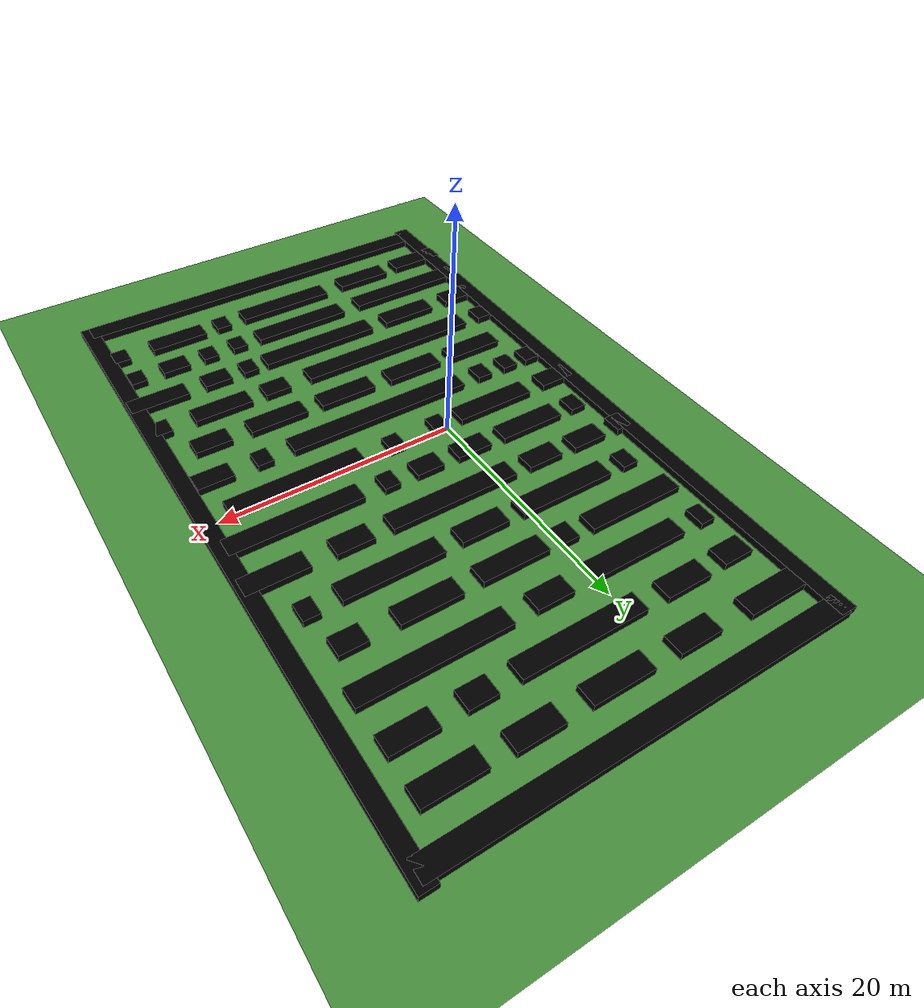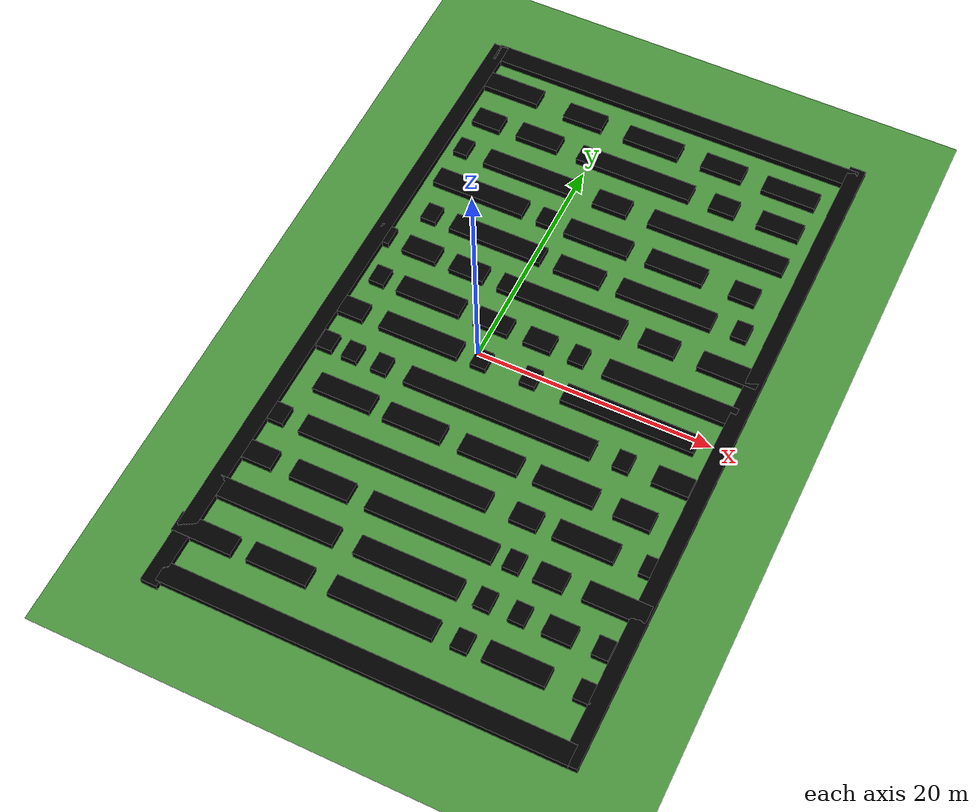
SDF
<sdf version="1.6">
 <world name="default">
  <light name="sun" type="directional">
   <pose>0 0 10 0 -0 0</pose>
   <diffuse>0.8 0.8 0.8 1</diffuse>
   <specular>0.1 0.1 0.1 1</specular>
   <attenuation>
    <range>1000</range>
    <constant>0.9</constant>
    <linear>0.01</linear>
    <quadratic>0.001</quadratic>
   </attenuation>
   <direction>-0.5 0.5 -1</direction>
  </light>
  <model name="ground_plane">
   <static>1</static>
   <link name="link">
    <collision name="collision">
     <geometry><plane><normal>0 0 1</normal><size>120 120</size></plane></geometry>
     <surface><friction><ode><mu>100</mu><mu2>50</mu2></ode></friction></surface>
    </collision>
    <visual name="visual">
     <cast_shadows>0</cast_shadows>
     <geometry><plane><normal>0 0 1</normal><size>120 120</size></plane></geometry>
     <material>
      <script><uri>file://media/materials/scripts/gazebo.material</uri><name>Gazebo/Grass</name></script>
     </material>
    </visual>
   </link>
  </model>
  <gravity>0 0 -9.8</gravity>
  <magnetic_field>6e-06 2.3e-05 -4.2e-05</magnetic_field>
  <atmosphere type="adiabatic"/>
  <physics name="default_physics" default="0" type="ode">
   <max_step_size>0.001</max_step_size>
   <real_time_factor>1</real_time_factor>
   <real_time_update_rate>1000</real_time_update_rate>
  </physics>
  <scene><ambient>0.4 0.4 0.4 1</ambient><background>0.7 0.7 0.7 1</background><shadows>1</shadows></scene>
  <spherical_coordinates>
   <surface_model>EARTH_WGS84</surface_model>
   <latitude_deg>0</latitude_deg>
   <longitude_deg>0</longitude_deg>
   <elevation>0</elevation>
   <heading_deg>0</heading_deg>
  </spherical_coordinates>
  <model name="crop_01_8_clone">
   <link name="crop_01_0::link_0">
    <inertial>
     <mass>10.9148</mass>
     <inertia><ixx>13.7036</ixx><ixy>0</ixy><ixz>0</ixz><iyy>702.087</iyy><iyz>0</iyz><izz>715.772</izz></inertia>
    </inertial>
    <visual name="visual">
     <geometry><box><size>10.6183 1.68705 1</size></box></geometry>
     <material>
      <ambient>0 1 0 1</ambient>
      <diffuse>0 0 0 1</diffuse>
      <specular>0.1 0.1 0.1 1</specular>
      <emissive>0 0 0 0</emissive>
     </material>
    </visual>
    <collision name="collision">
     <geometry><box><size>10.6183 1.68705 1</size></box></geometry>
     <surface>
      <friction>
       <ode><mu>1</mu><mu2>1</mu2><fdir1>0 0 0</fdir1><slip1>0</slip1><slip2>0</slip2></ode>
       <torsional>
        <coefficient>1</coefficient>
        <patch_radius>0</patch_radius>
        <surface_radius>0</surface_radius>
        <use_patch_radius>1</use_patch_radius>
        <ode><slip>0</slip></ode>
       </torsional>
      </friction>
      <bounce><restitution_coefficient>0</restitution_coefficient><threshold>1e+06</threshold></bounce>
      <contact>
       <collide_without_contact>0</collide_without_contact>
       <collide_without_contact_bitmask>1</collide_without_contact_bitmask>
       <collide_bitmask>1</collide_bitmask>
       <ode>
        <soft_cfm>0</soft_cfm>
        <soft_erp>0.2</soft_erp>
        <kp>1e+13</kp>
        <kd>1</kd>
        <max_vel>0.01</max_vel>
        <min_depth>0</min_depth>
       </ode>
       <bullet>
        <split_impulse>1</split_impulse>
        <split_impulse_penetration_threshold>-0.01</split_impulse_penetration_threshold>
        <soft_cfm>0</soft_cfm>
        <soft_erp>0.2</soft_erp>
        <kp>1e+13</kp>
        <kd>1</kd>
       </bullet>
      </contact>
     </surface>
    </collision>
   </link>
   <static>1</static>
   <pose>3.79308 -15.5752 0.050638 0 -0 0</pose>
  </model>
  <model name="crop_01_8_clone_0_clone_0_clone">
   <link name="crop_01_0::link_0">
    <inertial>
     <mass>10.9148</mass>
     <inertia><ixx>13.7036</ixx><ixy>0</ixy><ixz>0</ixz><iyy>702.087</iyy><iyz>0</iyz><izz>715.772</izz></inertia>
    </inertial>
    <visual name="visual">
     <geometry><box><size>6.96579 1.68705 1</size></box></geometry>
     <material>
      <ambient>0 1 0 1</ambient>
      <diffuse>0 0 0 1</diffuse>
      <specular>0.1 0.1 0.1 1</specular>
      <emissive>0 0 0 0</emissive>
     </material>
    </visual>
    <collision name="collision">
     <geometry><box><size>6.96579 1.68705 1</size></box></geometry>
     <surface>
      <friction>
       <ode><mu>1</mu><mu2>1</mu2><fdir1>0 0 0</fdir1><slip1>0</slip1><slip2>0</slip2></ode>
       <torsional>
        <coefficient>1</coefficient>
        <patch_radius>0</patch_radius>
        <surface_radius>0</surface_radius>
        <use_patch_radius>1</use_patch_radius>
        <ode><slip>0</slip></ode>
       </torsional>
      </friction>
      <bounce><restitution_coefficient>0</restitution_coefficient><threshold>1e+06</threshold></bounce>
      <contact>
       <collide_without_contact>0</collide_without_contact>
       <collide_without_contact_bitmask>1</collide_without_contact_bitmask>
       <collide_bitmask>1</collide_bitmask>
       <ode>
        <soft_cfm>0</soft_cfm>
        <soft_erp>0.2</soft_erp>
        <kp>1e+13</kp>
        <kd>1</kd>
        <max_vel>0.01</max_vel>
        <min_depth>0</min_depth>
       </ode>
       <bullet>
        <split_impulse>1</split_impulse>
        <split_impulse_penetration_threshold>-0.01</split_impulse_penetration_threshold>
        <soft_cfm>0</soft_cfm>
        <soft_erp>0.2</soft_erp>
        <kp>1e+13</kp>
        <kd>1</kd>
       </bullet>
      </contact>
     </surface>
    </collision>
   </link>
   <static>1</static>
   <pose>-4.73584 -0.562011 0.050638 0 -0 0</pose>
  </model>
  <model name="crop_01_8_clone_0_clone_0_clone_0">
   <link name="crop_01_0::link_0">
    <inertial>
     <mass>10.9148</mass>
     <inertia><ixx>13.7036</ixx><ixy>0</ixy><ixz>0</ixz><iyy>702.087</iyy><iyz>0</iyz><izz>715.772</izz></inertia>
    </inertial>
    <visual name="visual">
     <geometry><box><size>2.41149 1.68705 1</size></box></geometry>
     <material>
      <ambient>0 1 0 1</ambient>
      <diffuse>0 0 0 1</diffuse>
      <specular>0.1 0.1 0.1 1</specular>
      <emissive>0 0 0 0</emissive>
     </material>
    </visual>
    <collision name="collision">
     <geometry><box><size>2.41149 1.68705 1</size></box></geometry>
     <surface>
      <friction>
       <ode><mu>1</mu><mu2>1</mu2><fdir1>0 0 0</fdir1><slip1>0</slip1><slip2>0</slip2></ode>
       <torsional>
        <coefficient>1</coefficient>
        <patch_radius>0</patch_radius>
        <surface_radius>0</surface_radius>
        <use_patch_radius>1</use_patch_radius>
        <ode><slip>0</slip></ode>
       </torsional>
      </friction>
      <bounce><restitution_coefficient>0</restitution_coefficient><threshold>1e+06</threshold></bounce>
      <contact>
       <collide_without_contact>0</collide_without_contact>
       <collide_without_contact_bitmask>1</collide_without_contact_bitmask>
       <collide_bitmask>1</collide_bitmask>
       <ode>
        <soft_cfm>0</soft_cfm>
        <soft_erp>0.2</soft_erp>
        <kp>1e+13</kp>
        <kd>1</kd>
        <max_vel>0.01</max_vel>
        <min_depth>0</min_depth>
       </ode>
       <bullet>
        <split_impulse>1</split_impulse>
        <split_impulse_penetration_threshold>-0.01</split_impulse_penetration_threshold>
        <soft_cfm>0</soft_cfm>
        <soft_erp>0.2</soft_erp>
        <kp>1e+13</kp>
        <kd>1</kd>
       </bullet>
      </contact>
     </surface>
    </collision>
   </link>
   <static>1</static>
   <pose>4.01911 3.07059 0.050638 0 -0 0</pose>
  </model>
  <model name="crop_01_8_clone_0_clone_0_clone_1">
   <link name="crop_01_0::link_0">
    <inertial>
     <mass>10.9148</mass>
     <inertia><ixx>13.7036</ixx><ixy>0</ixy><ixz>0</ixz><iyy>702.087</iyy><iyz>0</iyz><izz>715.772</izz></inertia>
    </inertial>
    <visual name="visual">
     <geometry><box><size>10.9749 1.68705 1</size></box></geometry>
     <material>
      <ambient>0 1 0 1</ambient>
      <diffuse>0 0 0 1</diffuse>
      <specular>0.1 0.1 0.1 1</specular>
      <emissive>0 0 0 0</emissive>
     </material>
    </visual>
    <collision name="collision">
     <geometry><box><size>10.9749 1.68705 1</size></box></geometry>
     <surface>
      <friction>
       <ode><mu>1</mu><mu2>1</mu2><fdir1>0 0 0</fdir1><slip1>0</slip1><slip2>0</slip2></ode>
       <torsional>
        <coefficient>1</coefficient>
        <patch_radius>0</patch_radius>
        <surface_radius>0</surface_radius>
        <use_patch_radius>1</use_patch_radius>
        <ode><slip>0</slip></ode>
       </torsional>
      </friction>
      <bounce><restitution_coefficient>0</restitution_coefficient><threshold>1e+06</threshold></bounce>
      <contact>
       <collide_without_contact>0</collide_without_contact>
       <collide_without_contact_bitmask>1</collide_without_contact_bitmask>
       <collide_bitmask>1</collide_bitmask>
       <ode>
        <soft_cfm>0</soft_cfm>
        <soft_erp>0.2</soft_erp>
        <kp>1e+13</kp>
        <kd>1</kd>
        <max_vel>0.01</max_vel>
        <min_depth>0</min_depth>
       </ode>
       <bullet>
        <split_impulse>1</split_impulse>
        <split_impulse_penetration_threshold>-0.01</split_impulse_penetration_threshold>
        <soft_cfm>0</soft_cfm>
        <soft_erp>0.2</soft_erp>
        <kp>1e+13</kp>
        <kd>1</kd>
       </bullet>
      </contact>
     </surface>
    </collision>
   </link>
   <static>1</static>
   <pose>4.14547 6.85606 0.050638 0 -0 0</pose>
  </model>
  <model name="crop_01_8_clone_0_clone_0_clone_1_clone_clone">
   <link name="crop_01_0::link_0">
    <inertial>
     <mass>10.9148</mass>
     <inertia><ixx>13.7036</ixx><ixy>0</ixy><ixz>0</ixz><iyy>702.087</iyy><iyz>0</iyz><izz>715.772</izz></inertia>
    </inertial>
    <visual name="visual">
     <geometry><box><size>4.09046 1.68705 1</size></box></geometry>
     <material>
      <ambient>0 1 0 1</ambient>
      <diffuse>0 0 0 1</diffuse>
      <specular>0.1 0.1 0.1 1</specular>
      <emissive>0 0 0 0</emissive>
     </material>
    </visual>
    <collision name="collision">
     <geometry><box><size>4.09046 1.68705 1</size></box></geometry>
     <surface>
      <friction>
       <ode><mu>1</mu><mu2>1</mu2><fdir1>0 0 0</fdir1><slip1>0</slip1><slip2>0</slip2></ode>
       <torsional>
        <coefficient>1</coefficient>
        <patch_radius>0</patch_radius>
        <surface_radius>0</surface_radius>
        <use_patch_radius>1</use_patch_radius>
        <ode><slip>0</slip></ode>
       </torsional>
      </friction>
      <bounce><restitution_coefficient>0</restitution_coefficient><threshold>1e+06</threshold></bounce>
      <contact>
       <collide_without_contact>0</collide_without_contact>
       <collide_without_contact_bitmask>1</collide_without_contact_bitmask>
       <collide_bitmask>1</collide_bitmask>
       <ode>
        <soft_cfm>0</soft_cfm>
        <soft_erp>0.2</soft_erp>
        <kp>1e+13</kp>
        <kd>1</kd>
        <max_vel>0.01</max_vel>
        <min_depth>0</min_depth>
       </ode>
       <bullet>
        <split_impulse>1</split_impulse>
        <split_impulse_penetration_threshold>-0.01</split_impulse_penetration_threshold>
        <soft_cfm>0</soft_cfm>
        <soft_erp>0.2</soft_erp>
        <kp>1e+13</kp>
        <kd>1</kd>
       </bullet>
      </contact>
     </surface>
    </collision>
   </link>
   <static>1</static>
   <pose>4.07189 10.5095 0.050638 0 -0 0</pose>
  </model>
  <model name="crop_01_8_clone_0_clone_0_clone_1_clone_clone_clone">
   <link name="crop_01_0::link_0">
    <inertial>
     <mass>10.9148</mass>
     <inertia><ixx>13.7036</ixx><ixy>0</ixy><ixz>0</ixz><iyy>702.087</iyy><iyz>0</iyz><izz>715.772</izz></inertia>
    </inertial>
    <visual name="visual">
     <geometry><box><size>5.69318 1.68705 1</size></box></geometry>
     <material>
      <ambient>0 1 0 1</ambient>
      <diffuse>0 0 0 1</diffuse>
      <specular>0.1 0.1 0.1 1</specular>
      <emissive>0 0 0 0</emissive>
     </material>
    </visual>
    <collision name="collision">
     <geometry><box><size>5.69318 1.68705 1</size></box></geometry>
     <surface>
      <friction>
       <ode><mu>1</mu><mu2>1</mu2><fdir1>0 0 0</fdir1><slip1>0</slip1><slip2>0</slip2></ode>
       <torsional>
        <coefficient>1</coefficient>
        <patch_radius>0</patch_radius>
        <surface_radius>0</surface_radius>
        <use_patch_radius>1</use_patch_radius>
        <ode><slip>0</slip></ode>
       </torsional>
      </friction>
      <bounce><restitution_coefficient>0</restitution_coefficient><threshold>1e+06</threshold></bounce>
      <contact>
       <collide_without_contact>0</collide_without_contact>
       <collide_without_contact_bitmask>1</collide_without_contact_bitmask>
       <collide_bitmask>1</collide_bitmask>
       <ode>
        <soft_cfm>0</soft_cfm>
        <soft_erp>0.2</soft_erp>
        <kp>1e+13</kp>
        <kd>1</kd>
        <max_vel>0.01</max_vel>
        <min_depth>0</min_depth>
       </ode>
       <bullet>
        <split_impulse>1</split_impulse>
        <split_impulse_penetration_threshold>-0.01</split_impulse_penetration_threshold>
        <soft_cfm>0</soft_cfm>
        <soft_erp>0.2</soft_erp>
        <kp>1e+13</kp>
        <kd>1</kd>
       </bullet>
      </contact>
     </surface>
    </collision>
   </link>
   <static>1</static>
   <pose>4.07232 14.2098 0.050638 0 -0 0</pose>
  </model>
  <model name="crop_01_8_clone_0_clone_0_clone_1_clone_clone_clone_clone">
   <link name="crop_01_0::link_0">
    <inertial>
     <mass>10.9148</mass>
     <inertia><ixx>13.7036</ixx><ixy>0</ixy><ixz>0</ixz><iyy>702.087</iyy><iyz>0</iyz><izz>715.772</izz></inertia>
    </inertial>
    <visual name="visual">
     <geometry><box><size>3.0801 1.68705 1</size></box></geometry>
     <material>
      <ambient>0 1 0 1</ambient>
      <diffuse>0 0 0 1</diffuse>
      <specular>0.1 0.1 0.1 1</specular>
      <emissive>0 0 0 0</emissive>
     </material>
    </visual>
    <collision name="collision">
     <geometry><box><size>3.0801 1.68705 1</size></box></geometry>
     <surface>
      <friction>
       <ode><mu>1</mu><mu2>1</mu2><fdir1>0 0 0</fdir1><slip1>0</slip1><slip2>0</slip2></ode>
       <torsional>
        <coefficient>1</coefficient>
        <patch_radius>0</patch_radius>
        <surface_radius>0</surface_radius>
        <use_patch_radius>1</use_patch_radius>
        <ode><slip>0</slip></ode>
       </torsional>
      </friction>
      <bounce><restitution_coefficient>0</restitution_coefficient><threshold>1e+06</threshold></bounce>
      <contact>
       <collide_without_contact>0</collide_without_contact>
       <collide_without_contact_bitmask>1</collide_without_contact_bitmask>
       <collide_bitmask>1</collide_bitmask>
       <ode>
        <soft_cfm>0</soft_cfm>
        <soft_erp>0.2</soft_erp>
        <kp>1e+13</kp>
        <kd>1</kd>
        <max_vel>0.01</max_vel>
        <min_depth>0</min_depth>
       </ode>
       <bullet>
        <split_impulse>1</split_impulse>
        <split_impulse_penetration_threshold>-0.01</split_impulse_penetration_threshold>
        <soft_cfm>0</soft_cfm>
        <soft_erp>0.2</soft_erp>
        <kp>1e+13</kp>
        <kd>1</kd>
       </bullet>
      </contact>
     </surface>
    </collision>
   </link>
   <static>1</static>
   <pose>3.63993 18.0148 0.050638 0 -0 0</pose>
  </model>
  <model name="crop_01_8_clone_0_clone_0_clone_1_clone_clone_clone_clone_0">
   <link name="crop_01_0::link_0">
    <inertial>
     <mass>10.9148</mass>
     <inertia><ixx>13.7036</ixx><ixy>0</ixy><ixz>0</ixz><iyy>702.087</iyy><iyz>0</iyz><izz>715.772</izz></inertia>
    </inertial>
    <visual name="visual">
     <geometry><box><size>10.3295 1.68705 1</size></box></geometry>
     <material>
      <ambient>0 1 0 1</ambient>
      <diffuse>0 0 0 1</diffuse>
      <specular>0.1 0.1 0.1 1</specular>
      <emissive>0 0 0 0</emissive>
     </material>
    </visual>
    <collision name="collision">
     <geometry><box><size>10.3295 1.68705 1</size></box></geometry>
     <surface>
      <friction>
       <ode><mu>1</mu><mu2>1</mu2><fdir1>0 0 0</fdir1><slip1>0</slip1><slip2>0</slip2></ode>
       <torsional>
        <coefficient>1</coefficient>
        <patch_radius>0</patch_radius>
        <surface_radius>0</surface_radius>
        <use_patch_radius>1</use_patch_radius>
        <ode><slip>0</slip></ode>
       </torsional>
      </friction>
      <bounce><restitution_coefficient>0</restitution_coefficient><threshold>1e+06</threshold></bounce>
      <contact>
       <collide_without_contact>0</collide_without_contact>
       <collide_without_contact_bitmask>1</collide_without_contact_bitmask>
       <collide_bitmask>1</collide_bitmask>
       <ode>
        <soft_cfm>0</soft_cfm>
        <soft_erp>0.2</soft_erp>
        <kp>1e+13</kp>
        <kd>1</kd>
        <max_vel>0.01</max_vel>
        <min_depth>0</min_depth>
       </ode>
       <bullet>
        <split_impulse>1</split_impulse>
        <split_impulse_penetration_threshold>-0.01</split_impulse_penetration_threshold>
        <soft_cfm>0</soft_cfm>
        <soft_erp>0.2</soft_erp>
        <kp>1e+13</kp>
        <kd>1</kd>
       </bullet>
      </contact>
     </surface>
    </collision>
   </link>
   <static>1</static>
   <pose>4.08383 21.7323 0.050638 0 -0 0</pose>
  </model>
  <model name="crop_01_8_clone_0_clone_0_clone_1_clone_clone_clone_clone_0_clone">
   <link name="crop_01_0::link_0">
    <inertial>
     <mass>10.9148</mass>
     <inertia><ixx>13.7036</ixx><ixy>0</ixy><ixz>0</ixz><iyy>702.087</iyy><iyz>0</iyz><izz>715.772</izz></inertia>
    </inertial>
    <visual name="visual">
     <geometry><box><size>5.03328 1.68705 1</size></box></geometry>
     <material>
      <ambient>0 1 0 1</ambient>
      <diffuse>0 0 0 1</diffuse>
      <specular>0.1 0.1 0.1 1</specular>
      <emissive>0 0 0 0</emissive>
     </material>
    </visual>
    <collision name="collision">
     <geometry><box><size>5.03328 1.68705 1</size></box></geometry>
     <surface>
      <friction>
       <ode><mu>1</mu><mu2>1</mu2><fdir1>0 0 0</fdir1><slip1>0</slip1><slip2>0</slip2></ode>
       <torsional>
        <coefficient>1</coefficient>
        <patch_radius>0</patch_radius>
        <surface_radius>0</surface_radius>
        <use_patch_radius>1</use_patch_radius>
        <ode><slip>0</slip></ode>
       </torsional>
      </friction>
      <bounce><restitution_coefficient>0</restitution_coefficient><threshold>1e+06</threshold></bounce>
      <contact>
       <collide_without_contact>0</collide_without_contact>
       <collide_without_contact_bitmask>1</collide_without_contact_bitmask>
       <collide_bitmask>1</collide_bitmask>
       <ode>
        <soft_cfm>0</soft_cfm>
        <soft_erp>0.2</soft_erp>
        <kp>1e+13</kp>
        <kd>1</kd>
        <max_vel>0.01</max_vel>
        <min_depth>0</min_depth>
       </ode>
       <bullet>
        <split_impulse>1</split_impulse>
        <split_impulse_penetration_threshold>-0.01</split_impulse_penetration_threshold>
        <soft_cfm>0</soft_cfm>
        <soft_erp>0.2</soft_erp>
        <kp>1e+13</kp>
        <kd>1</kd>
       </bullet>
      </contact>
     </surface>
    </collision>
   </link>
   <static>1</static>
   <pose>4.15605 25.4436 0.050638 0 -0 0</pose>
  </model>
  <model name="crop_01_8_clone_0_clone_0_clone_1_clone_clone_clone_clone_0_clone_1">
   <link name="crop_01_0::link_0">
    <inertial>
     <mass>10.9148</mass>
     <inertia><ixx>13.7036</ixx><ixy>0</ixy><ixz>0</ixz><iyy>702.087</iyy><iyz>0</iyz><izz>715.772</izz></inertia>
    </inertial>
    <visual name="visual">
     <geometry><box><size>8.63139 1.68705 1</size></box></geometry>
     <material>
      <ambient>0 1 0 1</ambient>
      <diffuse>0 0 0 1</diffuse>
      <specular>0.1 0.1 0.1 1</specular>
      <emissive>0 0 0 0</emissive>
     </material>
    </visual>
    <collision name="collision">
     <geometry><box><size>8.63139 1.68705 1</size></box></geometry>
     <surface>
      <friction>
       <ode><mu>1</mu><mu2>1</mu2><fdir1>0 0 0</fdir1><slip1>0</slip1><slip2>0</slip2></ode>
       <torsional>
        <coefficient>1</coefficient>
        <patch_radius>0</patch_radius>
        <surface_radius>0</surface_radius>
        <use_patch_radius>1</use_patch_radius>
        <ode><slip>0</slip></ode>
       </torsional>
      </friction>
      <bounce><restitution_coefficient>0</restitution_coefficient><threshold>1e+06</threshold></bounce>
      <contact>
       <collide_without_contact>0</collide_without_contact>
       <collide_without_contact_bitmask>1</collide_without_contact_bitmask>
       <collide_bitmask>1</collide_bitmask>
       <ode>
        <soft_cfm>0</soft_cfm>
        <soft_erp>0.2</soft_erp>
        <kp>1e+13</kp>
        <kd>1</kd>
        <max_vel>0.01</max_vel>
        <min_depth>0</min_depth>
       </ode>
       <bullet>
        <split_impulse>1</split_impulse>
        <split_impulse_penetration_threshold>-0.01</split_impulse_penetration_threshold>
        <soft_cfm>0</soft_cfm>
        <soft_erp>0.2</soft_erp>
        <kp>1e+13</kp>
        <kd>1</kd>
       </bullet>
      </contact>
     </surface>
    </collision>
   </link>
   <static>1</static>
   <pose>3.80036 -19.2787 0.050638 0 -0 0</pose>
  </model>
  <model name="crop_01_8_clone_0_clone_0_clone_clone_0">
   <link name="crop_01_0::link_0">
    <inertial>
     <mass>10.9148</mass>
     <inertia><ixx>13.7036</ixx><ixy>0</ixy><ixz>0</ixz><iyy>702.087</iyy><iyz>0</iyz><izz>715.772</izz></inertia>
    </inertial>
    <visual name="visual">
     <geometry><box><size>11.274 1.68705 1</size></box></geometry>
     <material>
      <ambient>0 1 0 1</ambient>
      <diffuse>0 0 0 1</diffuse>
      <specular>0.1 0.1 0.1 1</specular>
      <emissive>0 0 0 0</emissive>
     </material>
    </visual>
    <collision name="collision">
     <geometry><box><size>11.274 1.68705 1</size></box></geometry>
     <surface>
      <friction>
       <ode><mu>1</mu><mu2>1</mu2><fdir1>0 0 0</fdir1><slip1>0</slip1><slip2>0</slip2></ode>
       <torsional>
        <coefficient>1</coefficient>
        <patch_radius>0</patch_radius>
        <surface_radius>0</surface_radius>
        <use_patch_radius>1</use_patch_radius>
        <ode><slip>0</slip></ode>
       </torsional>
      </friction>
      <bounce><restitution_coefficient>0</restitution_coefficient><threshold>1e+06</threshold></bounce>
      <contact>
       <collide_without_contact>0</collide_without_contact>
       <collide_without_contact_bitmask>1</collide_without_contact_bitmask>
       <collide_bitmask>1</collide_bitmask>
       <ode>
        <soft_cfm>0</soft_cfm>
        <soft_erp>0.2</soft_erp>
        <kp>1e+13</kp>
        <kd>1</kd>
        <max_vel>0.01</max_vel>
        <min_depth>0</min_depth>
       </ode>
       <bullet>
        <split_impulse>1</split_impulse>
        <split_impulse_penetration_threshold>-0.01</split_impulse_penetration_threshold>
        <soft_cfm>0</soft_cfm>
        <soft_erp>0.2</soft_erp>
        <kp>1e+13</kp>
        <kd>1</kd>
       </bullet>
      </contact>
     </surface>
    </collision>
   </link>
   <static>1</static>
   <pose>13.4072 -0.571304 0.050638 0 -0 0</pose>
  </model>
  <model name="crop_01_8_clone_0_clone">
   <link name="crop_01_0::link_0">
    <inertial>
     <mass>10.9148</mass>
     <inertia><ixx>13.7036</ixx><ixy>0</ixy><ixz>0</ixz><iyy>702.087</iyy><iyz>0</iyz><izz>715.772</izz></inertia>
    </inertial>
    <visual name="visual">
     <geometry><box><size>16.0862 1.68705 1</size></box></geometry>
     <material>
      <ambient>0 1 0 1</ambient>
      <diffuse>0 0 0 1</diffuse>
      <specular>0.1 0.1 0.1 1</specular>
      <emissive>0 0 0 0</emissive>
     </material>
    </visual>
    <collision name="collision">
     <geometry><box><size>16.0862 1.68705 1</size></box></geometry>
     <surface>
      <friction>
       <ode><mu>1</mu><mu2>1</mu2><fdir1>0 0 0</fdir1><slip1>0</slip1><slip2>0</slip2></ode>
       <torsional>
        <coefficient>1</coefficient>
        <patch_radius>0</patch_radius>
        <surface_radius>0</surface_radius>
        <use_patch_radius>1</use_patch_radius>
        <ode><slip>0</slip></ode>
       </torsional>
      </friction>
      <bounce><restitution_coefficient>0</restitution_coefficient><threshold>1e+06</threshold></bounce>
      <contact>
       <collide_without_contact>0</collide_without_contact>
       <collide_without_contact_bitmask>1</collide_without_contact_bitmask>
       <collide_bitmask>1</collide_bitmask>
       <ode>
        <soft_cfm>0</soft_cfm>
        <soft_erp>0.2</soft_erp>
        <kp>1e+13</kp>
        <kd>1</kd>
        <max_vel>0.01</max_vel>
        <min_depth>0</min_depth>
       </ode>
       <bullet>
        <split_impulse>1</split_impulse>
        <split_impulse_penetration_threshold>-0.01</split_impulse_penetration_threshold>
        <soft_cfm>0</soft_cfm>
        <soft_erp>0.2</soft_erp>
        <kp>1e+13</kp>
        <kd>1</kd>
       </bullet>
      </contact>
     </surface>
    </collision>
   </link>
   <static>1</static>
   <pose>3.99494 -4.3494 0.050638 0 -0 0</pose>
  </model>
  <model name="crop_01_8_clone_0_clone_0_clone_1_clone_clone_clone_clone_0_clone_clone">
   <link name="crop_01_0::link_0">
    <inertial>
     <mass>10.9148</mass>
     <inertia><ixx>13.7036</ixx><ixy>0</ixy><ixz>0</ixz><iyy>702.087</iyy><iyz>0</iyz><izz>715.772</izz></inertia>
    </inertial>
    <visual name="visual">
     <geometry><box><size>3.5821 1.68705 1</size></box></geometry>
     <material>
      <ambient>0 1 0 1</ambient>
      <diffuse>0 0 0 1</diffuse>
      <specular>0.1 0.1 0.1 1</specular>
      <emissive>0 0 0 0</emissive>
     </material>
    </visual>
    <collision name="collision">
     <geometry><box><size>3.5821 1.68705 1</size></box></geometry>
     <surface>
      <friction>
       <ode><mu>1</mu><mu2>1</mu2><fdir1>0 0 0</fdir1><slip1>0</slip1><slip2>0</slip2></ode>
       <torsional>
        <coefficient>1</coefficient>
        <patch_radius>0</patch_radius>
        <surface_radius>0</surface_radius>
        <use_patch_radius>1</use_patch_radius>
        <ode><slip>0</slip></ode>
       </torsional>
      </friction>
      <bounce><restitution_coefficient>0</restitution_coefficient><threshold>1e+06</threshold></bounce>
      <contact>
       <collide_without_contact>0</collide_without_contact>
       <collide_without_contact_bitmask>1</collide_without_contact_bitmask>
       <collide_bitmask>1</collide_bitmask>
       <ode>
        <soft_cfm>0</soft_cfm>
        <soft_erp>0.2</soft_erp>
        <kp>1e+13</kp>
        <kd>1</kd>
        <max_vel>0.01</max_vel>
        <min_depth>0</min_depth>
       </ode>
       <bullet>
        <split_impulse>1</split_impulse>
        <split_impulse_penetration_threshold>-0.01</split_impulse_penetration_threshold>
        <soft_cfm>0</soft_cfm>
        <soft_erp>0.2</soft_erp>
        <kp>1e+13</kp>
        <kd>1</kd>
       </bullet>
      </contact>
     </surface>
    </collision>
   </link>
   <static>1</static>
   <pose>-2.24203 25.508 0.050638 0 -0 0</pose>
  </model>
  <model name="crop_01_8_clone_0_clone_0_clone_1_clone_clone_clone_clone_0_clone_clone_clone">
   <link name="crop_01_0::link_0">
    <inertial>
     <mass>10.9148</mass>
     <inertia><ixx>13.7036</ixx><ixy>0</ixy><ixz>0</ixz><iyy>702.087</iyy><iyz>0</iyz><izz>715.772</izz></inertia>
    </inertial>
    <visual name="visual">
     <geometry><box><size>5.03328 1.68705 1</size></box></geometry>
     <material>
      <ambient>0 1 0 1</ambient>
      <diffuse>0 0 0 1</diffuse>
      <specular>0.1 0.1 0.1 1</specular>
      <emissive>0 0 0 0</emissive>
     </material>
    </visual>
    <collision name="collision">
     <geometry><box><size>5.03328 1.68705 1</size></box></geometry>
     <surface>
      <friction>
       <ode><mu>1</mu><mu2>1</mu2><fdir1>0 0 0</fdir1><slip1>0</slip1><slip2>0</slip2></ode>
       <torsional>
        <coefficient>1</coefficient>
        <patch_radius>0</patch_radius>
        <surface_radius>0</surface_radius>
        <use_patch_radius>1</use_patch_radius>
        <ode><slip>0</slip></ode>
       </torsional>
      </friction>
      <bounce><restitution_coefficient>0</restitution_coefficient><threshold>1e+06</threshold></bounce>
      <contact>
       <collide_without_contact>0</collide_without_contact>
       <collide_without_contact_bitmask>1</collide_without_contact_bitmask>
       <collide_bitmask>1</collide_bitmask>
       <ode>
        <soft_cfm>0</soft_cfm>
        <soft_erp>0.2</soft_erp>
        <kp>1e+13</kp>
        <kd>1</kd>
        <max_vel>0.01</max_vel>
        <min_depth>0</min_depth>
       </ode>
       <bullet>
        <split_impulse>1</split_impulse>
        <split_impulse_penetration_threshold>-0.01</split_impulse_penetration_threshold>
        <soft_cfm>0</soft_cfm>
        <soft_erp>0.2</soft_erp>
        <kp>1e+13</kp>
        <kd>1</kd>
       </bullet>
      </contact>
     </surface>
    </collision>
   </link>
   <static>1</static>
   <pose>-9.13815 25.7228 0.050638 0 -0 0</pose>
  </model>
  <model name="crop_01_8_clone_0_clone_0_clone_1_clone_clone_clone_clone_0_clone_clone_0">
   <link name="crop_01_0::link_0">
    <inertial>
     <mass>10.9148</mass>
     <inertia><ixx>13.7036</ixx><ixy>0</ixy><ixz>0</ixz><iyy>702.087</iyy><iyz>0</iyz><izz>715.772</izz></inertia>
    </inertial>
    <visual name="visual">
     <geometry><box><size>3.71638 1.68705 1</size></box></geometry>
     <material>
      <ambient>0 1 0 1</ambient>
      <diffuse>0 0 0 1</diffuse>
      <specular>0.1 0.1 0.1 1</specular>
      <emissive>0 0 0 0</emissive>
     </material>
    </visual>
    <collision name="collision">
     <geometry><box><size>3.71638 1.68705 1</size></box></geometry>
     <surface>
      <friction>
       <ode><mu>1</mu><mu2>1</mu2><fdir1>0 0 0</fdir1><slip1>0</slip1><slip2>0</slip2></ode>
       <torsional>
        <coefficient>1</coefficient>
        <patch_radius>0</patch_radius>
        <surface_radius>0</surface_radius>
        <use_patch_radius>1</use_patch_radius>
        <ode><slip>0</slip></ode>
       </torsional>
      </friction>
      <bounce><restitution_coefficient>0</restitution_coefficient><threshold>1e+06</threshold></bounce>
      <contact>
       <collide_without_contact>0</collide_without_contact>
       <collide_without_contact_bitmask>1</collide_without_contact_bitmask>
       <collide_bitmask>1</collide_bitmask>
       <ode>
        <soft_cfm>0</soft_cfm>
        <soft_erp>0.2</soft_erp>
        <kp>1e+13</kp>
        <kd>1</kd>
        <max_vel>0.01</max_vel>
        <min_depth>0</min_depth>
       </ode>
       <bullet>
        <split_impulse>1</split_impulse>
        <split_impulse_penetration_threshold>-0.01</split_impulse_penetration_threshold>
        <soft_cfm>0</soft_cfm>
        <soft_erp>0.2</soft_erp>
        <kp>1e+13</kp>
        <kd>1</kd>
       </bullet>
      </contact>
     </surface>
    </collision>
   </link>
   <static>1</static>
   <pose>10.6039 25.4804 0.050638 0 -0 0</pose>
  </model>
  <model name="crop_01_8_clone_0_clone_0_clone_1_clone_clone_clone_clone_0_clone_clone_0_clone">
   <link name="crop_01_0::link_0">
    <inertial>
     <mass>10.9148</mass>
     <inertia><ixx>13.7036</ixx><ixy>0</ixy><ixz>0</ixz><iyy>702.087</iyy><iyz>0</iyz><izz>715.772</izz></inertia>
    </inertial>
    <visual name="visual">
     <geometry><box><size>4.76608 1.68705 1</size></box></geometry>
     <material>
      <ambient>0 1 0 1</ambient>
      <diffuse>0 0 0 1</diffuse>
      <specular>0.1 0.1 0.1 1</specular>
      <emissive>0 0 0 0</emissive>
     </material>
    </visual>
    <collision name="collision">
     <geometry><box><size>4.76608 1.68705 1</size></box></geometry>
     <surface>
      <friction>
       <ode><mu>1</mu><mu2>1</mu2><fdir1>0 0 0</fdir1><slip1>0</slip1><slip2>0</slip2></ode>
       <torsional>
        <coefficient>1</coefficient>
        <patch_radius>0</patch_radius>
        <surface_radius>0</surface_radius>
        <use_patch_radius>1</use_patch_radius>
        <ode><slip>0</slip></ode>
       </torsional>
      </friction>
      <bounce><restitution_coefficient>0</restitution_coefficient><threshold>1e+06</threshold></bounce>
      <contact>
       <collide_without_contact>0</collide_without_contact>
       <collide_without_contact_bitmask>1</collide_without_contact_bitmask>
       <collide_bitmask>1</collide_bitmask>
       <ode>
        <soft_cfm>0</soft_cfm>
        <soft_erp>0.2</soft_erp>
        <kp>1e+13</kp>
        <kd>1</kd>
        <max_vel>0.01</max_vel>
        <min_depth>0</min_depth>
       </ode>
       <bullet>
        <split_impulse>1</split_impulse>
        <split_impulse_penetration_threshold>-0.01</split_impulse_penetration_threshold>
        <soft_cfm>0</soft_cfm>
        <soft_erp>0.2</soft_erp>
        <kp>1e+13</kp>
        <kd>1</kd>
       </bullet>
      </contact>
     </surface>
    </collision>
   </link>
   <static>1</static>
   <pose>16.6768 25.3873 0.050638 0 -0 0</pose>
  </model>
  <model name="crop_01_8_clone_0_clone_0_clone_1_clone_clone_clone_clone_0_clone_clone_0_clone_0">
   <link name="crop_01_0::link_0">
    <inertial>
     <mass>10.9148</mass>
     <inertia><ixx>13.7036</ixx><ixy>0</ixy><ixz>0</ixz><iyy>702.087</iyy><iyz>0</iyz><izz>715.772</izz></inertia>
    </inertial>
    <visual name="visual">
     <geometry><box><size>2.29963 1.68705 1</size></box></geometry>
     <material>
      <ambient>0 1 0 1</ambient>
      <diffuse>0 0 0 1</diffuse>
      <specular>0.1 0.1 0.1 1</specular>
      <emissive>0 0 0 0</emissive>
     </material>
    </visual>
    <collision name="collision">
     <geometry><box><size>2.29963 1.68705 1</size></box></geometry>
     <surface>
      <friction>
       <ode><mu>1</mu><mu2>1</mu2><fdir1>0 0 0</fdir1><slip1>0</slip1><slip2>0</slip2></ode>
       <torsional>
        <coefficient>1</coefficient>
        <patch_radius>0</patch_radius>
        <surface_radius>0</surface_radius>
        <use_patch_radius>1</use_patch_radius>
        <ode><slip>0</slip></ode>
       </torsional>
      </friction>
      <bounce><restitution_coefficient>0</restitution_coefficient><threshold>1e+06</threshold></bounce>
      <contact>
       <collide_without_contact>0</collide_without_contact>
       <collide_without_contact_bitmask>1</collide_without_contact_bitmask>
       <collide_bitmask>1</collide_bitmask>
       <ode>
        <soft_cfm>0</soft_cfm>
        <soft_erp>0.2</soft_erp>
        <kp>1e+13</kp>
        <kd>1</kd>
        <max_vel>0.01</max_vel>
        <min_depth>0</min_depth>
       </ode>
       <bullet>
        <split_impulse>1</split_impulse>
        <split_impulse_penetration_threshold>-0.01</split_impulse_penetration_threshold>
        <soft_cfm>0</soft_cfm>
        <soft_erp>0.2</soft_erp>
        <kp>1e+13</kp>
        <kd>1</kd>
       </bullet>
      </contact>
     </surface>
    </collision>
   </link>
   <static>1</static>
   <pose>12.1672 21.7564 0.050638 0 -0 0</pose>
  </model>
  <model name="crop_01_8_clone_0_clone_0_clone_1_clone_clone_clone_clone_0_clone_clone_0_clone_1">
   <link name="crop_01_0::link_0">
    <inertial>
     <mass>10.9148</mass>
     <inertia><ixx>13.7036</ixx><ixy>0</ixy><ixz>0</ixz><iyy>702.087</iyy><iyz>0</iyz><izz>715.772</izz></inertia>
    </inertial>
    <visual name="visual">
     <geometry><box><size>3.71639 1.68705 1</size></box></geometry>
     <material>
      <ambient>0 1 0 1</ambient>
      <diffuse>0 0 0 1</diffuse>
      <specular>0.1 0.1 0.1 1</specular>
      <emissive>0 0 0 0</emissive>
     </material>
    </visual>
    <collision name="collision">
     <geometry><box><size>3.71639 1.68705 1</size></box></geometry>
     <surface>
      <friction>
       <ode><mu>1</mu><mu2>1</mu2><fdir1>0 0 0</fdir1><slip1>0</slip1><slip2>0</slip2></ode>
       <torsional>
        <coefficient>1</coefficient>
        <patch_radius>0</patch_radius>
        <surface_radius>0</surface_radius>
        <use_patch_radius>1</use_patch_radius>
        <ode><slip>0</slip></ode>
       </torsional>
      </friction>
      <bounce><restitution_coefficient>0</restitution_coefficient><threshold>1e+06</threshold></bounce>
      <contact>
       <collide_without_contact>0</collide_without_contact>
       <collide_without_contact_bitmask>1</collide_without_contact_bitmask>
       <collide_bitmask>1</collide_bitmask>
       <ode>
        <soft_cfm>0</soft_cfm>
        <soft_erp>0.2</soft_erp>
        <kp>1e+13</kp>
        <kd>1</kd>
        <max_vel>0.01</max_vel>
        <min_depth>0</min_depth>
       </ode>
       <bullet>
        <split_impulse>1</split_impulse>
        <split_impulse_penetration_threshold>-0.01</split_impulse_penetration_threshold>
        <soft_cfm>0</soft_cfm>
        <soft_erp>0.2</soft_erp>
        <kp>1e+13</kp>
        <kd>1</kd>
       </bullet>
      </contact>
     </surface>
    </collision>
   </link>
   <static>1</static>
   <pose>17.1401 21.789 0.050638 0 -0 0</pose>
  </model>
  <model name="crop_01_8_clone_0_clone_0_clone_1_clone_clone_clone_clone_0_clone_clone_clone_clone">
   <link name="crop_01_0::link_0">
    <inertial>
     <mass>10.9148</mass>
     <inertia><ixx>13.7036</ixx><ixy>0</ixy><ixz>0</ixz><iyy>702.087</iyy><iyz>0</iyz><izz>715.772</izz></inertia>
    </inertial>
    <visual name="visual">
     <geometry><box><size>3.87175 1.68705 1</size></box></geometry>
     <material>
      <ambient>0 1 0 1</ambient>
      <diffuse>0 0 0 1</diffuse>
      <specular>0.1 0.1 0.1 1</specular>
      <emissive>0 0 0 0</emissive>
     </material>
    </visual>
    <collision name="collision">
     <geometry><box><size>3.87175 1.68705 1</size></box></geometry>
     <surface>
      <friction>
       <ode><mu>1</mu><mu2>1</mu2><fdir1>0 0 0</fdir1><slip1>0</slip1><slip2>0</slip2></ode>
       <torsional>
        <coefficient>1</coefficient>
        <patch_radius>0</patch_radius>
        <surface_radius>0</surface_radius>
        <use_patch_radius>1</use_patch_radius>
        <ode><slip>0</slip></ode>
       </torsional>
      </friction>
      <bounce><restitution_coefficient>0</restitution_coefficient><threshold>1e+06</threshold></bounce>
      <contact>
       <collide_without_contact>0</collide_without_contact>
       <collide_without_contact_bitmask>1</collide_without_contact_bitmask>
       <collide_bitmask>1</collide_bitmask>
       <ode>
        <soft_cfm>0</soft_cfm>
        <soft_erp>0.2</soft_erp>
        <kp>1e+13</kp>
        <kd>1</kd>
        <max_vel>0.01</max_vel>
        <min_depth>0</min_depth>
       </ode>
       <bullet>
        <split_impulse>1</split_impulse>
        <split_impulse_penetration_threshold>-0.01</split_impulse_penetration_threshold>
        <soft_cfm>0</soft_cfm>
        <soft_erp>0.2</soft_erp>
        <kp>1e+13</kp>
        <kd>1</kd>
       </bullet>
      </contact>
     </surface>
    </collision>
   </link>
   <static>1</static>
   <pose>-4.85078 21.8054 0.050638 0 -0 0</pose>
  </model>
  <model name="crop_01_8_clone_0_clone_0_clone_1_clone_clone_clone_clone_0_clone_clone_clone_clone_clone">
   <link name="crop_01_0::link_0">
    <inertial>
     <mass>10.9148</mass>
     <inertia><ixx>13.7036</ixx><ixy>0</ixy><ixz>0</ixz><iyy>702.087</iyy><iyz>0</iyz><izz>715.772</izz></inertia>
    </inertial>
    <visual name="visual">
     <geometry><box><size>2.58338 1.68705 1</size></box></geometry>
     <material>
      <ambient>0 1 0 1</ambient>
      <diffuse>0 0 0 1</diffuse>
      <specular>0.1 0.1 0.1 1</specular>
      <emissive>0 0 0 0</emissive>
     </material>
    </visual>
    <collision name="collision">
     <geometry><box><size>2.58338 1.68705 1</size></box></geometry>
     <surface>
      <friction>
       <ode><mu>1</mu><mu2>1</mu2><fdir1>0 0 0</fdir1><slip1>0</slip1><slip2>0</slip2></ode>
       <torsional>
        <coefficient>1</coefficient>
        <patch_radius>0</patch_radius>
        <surface_radius>0</surface_radius>
        <use_patch_radius>1</use_patch_radius>
        <ode><slip>0</slip></ode>
       </torsional>
      </friction>
      <bounce><restitution_coefficient>0</restitution_coefficient><threshold>1e+06</threshold></bounce>
      <contact>
       <collide_without_contact>0</collide_without_contact>
       <collide_without_contact_bitmask>1</collide_without_contact_bitmask>
       <collide_bitmask>1</collide_bitmask>
       <ode>
        <soft_cfm>0</soft_cfm>
        <soft_erp>0.2</soft_erp>
        <kp>1e+13</kp>
        <kd>1</kd>
        <max_vel>0.01</max_vel>
        <min_depth>0</min_depth>
       </ode>
       <bullet>
        <split_impulse>1</split_impulse>
        <split_impulse_penetration_threshold>-0.01</split_impulse_penetration_threshold>
        <soft_cfm>0</soft_cfm>
        <soft_erp>0.2</soft_erp>
        <kp>1e+13</kp>
        <kd>1</kd>
       </bullet>
      </contact>
     </surface>
    </collision>
   </link>
   <static>1</static>
   <pose>-9.57706 21.6971 0.050638 0 -0 0</pose>
  </model>
  <model name="crop_01_8_clone_0_clone_0_clone_1_clone_clone_clone_clone_0_clone_clone_1">
   <link name="crop_01_0::link_0">
    <inertial>
     <mass>10.9148</mass>
     <inertia><ixx>13.7036</ixx><ixy>0</ixy><ixz>0</ixz><iyy>702.087</iyy><iyz>0</iyz><izz>715.772</izz></inertia>
    </inertial>
    <visual name="visual">
     <geometry><box><size>8.14863 1.68705 1</size></box></geometry>
     <material>
      <ambient>0 1 0 1</ambient>
      <diffuse>0 0 0 1</diffuse>
      <specular>0.1 0.1 0.1 1</specular>
      <emissive>0 0 0 0</emissive>
     </material>
    </visual>
    <collision name="collision">
     <geometry><box><size>8.14863 1.68705 1</size></box></geometry>
     <surface>
      <friction>
       <ode><mu>1</mu><mu2>1</mu2><fdir1>0 0 0</fdir1><slip1>0</slip1><slip2>0</slip2></ode>
       <torsional>
        <coefficient>1</coefficient>
        <patch_radius>0</patch_radius>
        <surface_radius>0</surface_radius>
        <use_patch_radius>1</use_patch_radius>
        <ode><slip>0</slip></ode>
       </torsional>
      </friction>
      <bounce><restitution_coefficient>0</restitution_coefficient><threshold>1e+06</threshold></bounce>
      <contact>
       <collide_without_contact>0</collide_without_contact>
       <collide_without_contact_bitmask>1</collide_without_contact_bitmask>
       <collide_bitmask>1</collide_bitmask>
       <ode>
        <soft_cfm>0</soft_cfm>
        <soft_erp>0.2</soft_erp>
        <kp>1e+13</kp>
        <kd>1</kd>
        <max_vel>0.01</max_vel>
        <min_depth>0</min_depth>
       </ode>
       <bullet>
        <split_impulse>1</split_impulse>
        <split_impulse_penetration_threshold>-0.01</split_impulse_penetration_threshold>
        <soft_cfm>0</soft_cfm>
        <soft_erp>0.2</soft_erp>
        <kp>1e+13</kp>
        <kd>1</kd>
       </bullet>
      </contact>
     </surface>
    </collision>
   </link>
   <static>1</static>
   <pose>-3.92943 17.9844 0.050638 0 -0 0</pose>
  </model>
  <model name="crop_01_8_clone_0_clone_0_clone_1_clone_clone_clone_clone_0_clone_clone_clone_clone_clone_0">
   <link name="crop_01_0::link_0">
    <inertial>
     <mass>10.9148</mass>
     <inertia><ixx>13.7036</ixx><ixy>0</ixy><ixz>0</ixz><iyy>702.087</iyy><iyz>0</iyz><izz>715.772</izz></inertia>
    </inertial>
    <visual name="visual">
     <geometry><box><size>1.25333 1.68705 1</size></box></geometry>
     <material>
      <ambient>0 1 0 1</ambient>
      <diffuse>0 0 0 1</diffuse>
      <specular>0.1 0.1 0.1 1</specular>
      <emissive>0 0 0 0</emissive>
     </material>
    </visual>
    <collision name="collision">
     <geometry><box><size>1.25333 1.68705 1</size></box></geometry>
     <surface>
      <friction>
       <ode><mu>1</mu><mu2>1</mu2><fdir1>0 0 0</fdir1><slip1>0</slip1><slip2>0</slip2></ode>
       <torsional>
        <coefficient>1</coefficient>
        <patch_radius>0</patch_radius>
        <surface_radius>0</surface_radius>
        <use_patch_radius>1</use_patch_radius>
        <ode><slip>0</slip></ode>
       </torsional>
      </friction>
      <bounce><restitution_coefficient>0</restitution_coefficient><threshold>1e+06</threshold></bounce>
      <contact>
       <collide_without_contact>0</collide_without_contact>
       <collide_without_contact_bitmask>1</collide_without_contact_bitmask>
       <collide_bitmask>1</collide_bitmask>
       <ode>
        <soft_cfm>0</soft_cfm>
        <soft_erp>0.2</soft_erp>
        <kp>1e+13</kp>
        <kd>1</kd>
        <max_vel>0.01</max_vel>
        <min_depth>0</min_depth>
       </ode>
       <bullet>
        <split_impulse>1</split_impulse>
        <split_impulse_penetration_threshold>-0.01</split_impulse_penetration_threshold>
        <soft_cfm>0</soft_cfm>
        <soft_erp>0.2</soft_erp>
        <kp>1e+13</kp>
        <kd>1</kd>
       </bullet>
      </contact>
     </surface>
    </collision>
   </link>
   <static>1</static>
   <pose>-10.2372 18.0651 0.050638 0 -0 0</pose>
  </model>
  <model name="crop_01_8_clone_0_clone_0_clone_1_clone_clone_clone_clone_0_clone_clone_2">
   <link name="crop_01_0::link_0">
    <inertial>
     <mass>10.9148</mass>
     <inertia><ixx>13.7036</ixx><ixy>0</ixy><ixz>0</ixz><iyy>702.087</iyy><iyz>0</iyz><izz>715.772</izz></inertia>
    </inertial>
    <visual name="visual">
     <geometry><box><size>11.9696 1.68705 1</size></box></geometry>
     <material>
      <ambient>0 1 0 1</ambient>
      <diffuse>0 0 0 1</diffuse>
      <specular>0.1 0.1 0.1 1</specular>
      <emissive>0 0 0 0</emissive>
     </material>
    </visual>
    <collision name="collision">
     <geometry><box><size>11.9696 1.68705 1</size></box></geometry>
     <surface>
      <friction>
       <ode><mu>1</mu><mu2>1</mu2><fdir1>0 0 0</fdir1><slip1>0</slip1><slip2>0</slip2></ode>
       <torsional>
        <coefficient>1</coefficient>
        <patch_radius>0</patch_radius>
        <surface_radius>0</surface_radius>
        <use_patch_radius>1</use_patch_radius>
        <ode><slip>0</slip></ode>
       </torsional>
      </friction>
      <bounce><restitution_coefficient>0</restitution_coefficient><threshold>1e+06</threshold></bounce>
      <contact>
       <collide_without_contact>0</collide_without_contact>
       <collide_without_contact_bitmask>1</collide_without_contact_bitmask>
       <collide_bitmask>1</collide_bitmask>
       <ode>
        <soft_cfm>0</soft_cfm>
        <soft_erp>0.2</soft_erp>
        <kp>1e+13</kp>
        <kd>1</kd>
        <max_vel>0.01</max_vel>
        <min_depth>0</min_depth>
       </ode>
       <bullet>
        <split_impulse>1</split_impulse>
        <split_impulse_penetration_threshold>-0.01</split_impulse_penetration_threshold>
        <soft_cfm>0</soft_cfm>
        <soft_erp>0.2</soft_erp>
        <kp>1e+13</kp>
        <kd>1</kd>
       </bullet>
      </contact>
     </surface>
    </collision>
   </link>
   <static>1</static>
   <pose>13.0806 18.0451 0.050638 0 -0 0</pose>
  </model>
  <model name="crop_01_8_clone_0_clone_0_clone_1_clone_clone_clone_clone_0_clone_clone_3">
   <link name="crop_01_0::link_0">
    <inertial>
     <mass>10.9148</mass>
     <inertia><ixx>13.7036</ixx><ixy>0</ixy><ixz>0</ixz><iyy>702.087</iyy><iyz>0</iyz><izz>715.772</izz></inertia>
    </inertial>
    <visual name="visual">
     <geometry><box><size>5.03328 1.68705 1</size></box></geometry>
     <material>
      <ambient>0 1 0 1</ambient>
      <diffuse>0 0 0 1</diffuse>
      <specular>0.1 0.1 0.1 1</specular>
      <emissive>0 0 0 0</emissive>
     </material>
    </visual>
    <collision name="collision">
     <geometry><box><size>5.03328 1.68705 1</size></box></geometry>
     <surface>
      <friction>
       <ode><mu>1</mu><mu2>1</mu2><fdir1>0 0 0</fdir1><slip1>0</slip1><slip2>0</slip2></ode>
       <torsional>
        <coefficient>1</coefficient>
        <patch_radius>0</patch_radius>
        <surface_radius>0</surface_radius>
        <use_patch_radius>1</use_patch_radius>
        <ode><slip>0</slip></ode>
       </torsional>
      </friction>
      <bounce><restitution_coefficient>0</restitution_coefficient><threshold>1e+06</threshold></bounce>
      <contact>
       <collide_without_contact>0</collide_without_contact>
       <collide_without_contact_bitmask>1</collide_without_contact_bitmask>
       <collide_bitmask>1</collide_bitmask>
       <ode>
        <soft_cfm>0</soft_cfm>
        <soft_erp>0.2</soft_erp>
        <kp>1e+13</kp>
        <kd>1</kd>
        <max_vel>0.01</max_vel>
        <min_depth>0</min_depth>
       </ode>
       <bullet>
        <split_impulse>1</split_impulse>
        <split_impulse_penetration_threshold>-0.01</split_impulse_penetration_threshold>
        <soft_cfm>0</soft_cfm>
        <soft_erp>0.2</soft_erp>
        <kp>1e+13</kp>
        <kd>1</kd>
       </bullet>
      </contact>
     </surface>
    </collision>
   </link>
   <static>1</static>
   <pose>11.0347 14.261 0.050638 0 -0 0</pose>
  </model>
  <model name="crop_01_8_clone_0_clone_0_clone_1_clone_clone_clone_clone_0_clone_clone_4">
   <link name="crop_01_0::link_0">
    <inertial>
     <mass>10.9148</mass>
     <inertia><ixx>13.7036</ixx><ixy>0</ixy><ixz>0</ixz><iyy>702.087</iyy><iyz>0</iyz><izz>715.772</izz></inertia>
    </inertial>
    <visual name="visual">
     <geometry><box><size>8.26711 1.68705 1</size></box></geometry>
     <material>
      <ambient>0 1 0 1</ambient>
      <diffuse>0 0 0 1</diffuse>
      <specular>0.1 0.1 0.1 1</specular>
      <emissive>0 0 0 0</emissive>
     </material>
    </visual>
    <collision name="collision">
     <geometry><box><size>8.26711 1.68705 1</size></box></geometry>
     <surface>
      <friction>
       <ode><mu>1</mu><mu2>1</mu2><fdir1>0 0 0</fdir1><slip1>0</slip1><slip2>0</slip2></ode>
       <torsional>
        <coefficient>1</coefficient>
        <patch_radius>0</patch_radius>
        <surface_radius>0</surface_radius>
        <use_patch_radius>1</use_patch_radius>
        <ode><slip>0</slip></ode>
       </torsional>
      </friction>
      <bounce><restitution_coefficient>0</restitution_coefficient><threshold>1e+06</threshold></bounce>
      <contact>
       <collide_without_contact>0</collide_without_contact>
       <collide_without_contact_bitmask>1</collide_without_contact_bitmask>
       <collide_bitmask>1</collide_bitmask>
       <ode>
        <soft_cfm>0</soft_cfm>
        <soft_erp>0.2</soft_erp>
        <kp>1e+13</kp>
        <kd>1</kd>
        <max_vel>0.01</max_vel>
        <min_depth>0</min_depth>
       </ode>
       <bullet>
        <split_impulse>1</split_impulse>
        <split_impulse_penetration_threshold>-0.01</split_impulse_penetration_threshold>
        <soft_cfm>0</soft_cfm>
        <soft_erp>0.2</soft_erp>
        <kp>1e+13</kp>
        <kd>1</kd>
       </bullet>
      </contact>
     </surface>
    </collision>
   </link>
   <static>1</static>
   <pose>-6.77935 14.3691 0.050638 0 -0 0</pose>
  </model>
  <model name="crop_01_8_clone_0_clone_0_clone_1_clone_clone_clone_clone_clone">
   <link name="crop_01_0::link_0">
    <inertial>
     <mass>10.9148</mass>
     <inertia><ixx>13.7036</ixx><ixy>0</ixy><ixz>0</ixz><iyy>702.087</iyy><iyz>0</iyz><izz>715.772</izz></inertia>
    </inertial>
    <visual name="visual">
     <geometry><box><size>1.36286 1.68705 1</size></box></geometry>
     <material>
      <ambient>0 1 0 1</ambient>
      <diffuse>0 0 0 1</diffuse>
      <specular>0.1 0.1 0.1 1</specular>
      <emissive>0 0 0 0</emissive>
     </material>
    </visual>
    <collision name="collision">
     <geometry><box><size>1.36286 1.68705 1</size></box></geometry>
     <surface>
      <friction>
       <ode><mu>1</mu><mu2>1</mu2><fdir1>0 0 0</fdir1><slip1>0</slip1><slip2>0</slip2></ode>
       <torsional>
        <coefficient>1</coefficient>
        <patch_radius>0</patch_radius>
        <surface_radius>0</surface_radius>
        <use_patch_radius>1</use_patch_radius>
        <ode><slip>0</slip></ode>
       </torsional>
      </friction>
      <bounce><restitution_coefficient>0</restitution_coefficient><threshold>1e+06</threshold></bounce>
      <contact>
       <collide_without_contact>0</collide_without_contact>
       <collide_without_contact_bitmask>1</collide_without_contact_bitmask>
       <collide_bitmask>1</collide_bitmask>
       <ode>
        <soft_cfm>0</soft_cfm>
        <soft_erp>0.2</soft_erp>
        <kp>1e+13</kp>
        <kd>1</kd>
        <max_vel>0.01</max_vel>
        <min_depth>0</min_depth>
       </ode>
       <bullet>
        <split_impulse>1</split_impulse>
        <split_impulse_penetration_threshold>-0.01</split_impulse_penetration_threshold>
        <soft_cfm>0</soft_cfm>
        <soft_erp>0.2</soft_erp>
        <kp>1e+13</kp>
        <kd>1</kd>
       </bullet>
      </contact>
     </surface>
    </collision>
   </link>
   <static>1</static>
   <pose>-0.673769 14.3056 0.050638 0 -0 0</pose>
  </model>
  <model name="crop_01_8_clone_0_clone_0_clone_1_clone_clone_clone_clone_0_clone_clone_0_clone_0_clone">
   <link name="crop_01_0::link_0">
    <inertial>
     <mass>10.9148</mass>
     <inertia><ixx>13.7036</ixx><ixy>0</ixy><ixz>0</ixz><iyy>702.087</iyy><iyz>0</iyz><izz>715.772</izz></inertia>
    </inertial>
    <visual name="visual">
     <geometry><box><size>2.29963 1.68705 1</size></box></geometry>
     <material>
      <ambient>0 1 0 1</ambient>
      <diffuse>0 0 0 1</diffuse>
      <specular>0.1 0.1 0.1 1</specular>
      <emissive>0 0 0 0</emissive>
     </material>
    </visual>
    <collision name="collision">
     <geometry><box><size>2.29963 1.68705 1</size></box></geometry>
     <surface>
      <friction>
       <ode><mu>1</mu><mu2>1</mu2><fdir1>0 0 0</fdir1><slip1>0</slip1><slip2>0</slip2></ode>
       <torsional>
        <coefficient>1</coefficient>
        <patch_radius>0</patch_radius>
        <surface_radius>0</surface_radius>
        <use_patch_radius>1</use_patch_radius>
        <ode><slip>0</slip></ode>
       </torsional>
      </friction>
      <bounce><restitution_coefficient>0</restitution_coefficient><threshold>1e+06</threshold></bounce>
      <contact>
       <collide_without_contact>0</collide_without_contact>
       <collide_without_contact_bitmask>1</collide_without_contact_bitmask>
       <collide_bitmask>1</collide_bitmask>
       <ode>
        <soft_cfm>0</soft_cfm>
        <soft_erp>0.2</soft_erp>
        <kp>1e+13</kp>
        <kd>1</kd>
        <max_vel>0.01</max_vel>
        <min_depth>0</min_depth>
       </ode>
       <bullet>
        <split_impulse>1</split_impulse>
        <split_impulse_penetration_threshold>-0.01</split_impulse_penetration_threshold>
        <soft_cfm>0</soft_cfm>
        <soft_erp>0.2</soft_erp>
        <kp>1e+13</kp>
        <kd>1</kd>
       </bullet>
      </contact>
     </surface>
    </collision>
   </link>
   <static>1</static>
   <pose>17.0148 14.2347 0.050638 0 -0 0</pose>
  </model>
  <model name="crop_01_8_clone_0_clone_0_clone_1_clone_clone_clone_clone_0_clone_clone_4_clone">
   <link name="crop_01_0::link_0">
    <inertial>
     <mass>10.9148</mass>
     <inertia><ixx>13.7036</ixx><ixy>0</ixy><ixz>0</ixz><iyy>702.087</iyy><iyz>0</iyz><izz>715.772</izz></inertia>
    </inertial>
    <visual name="visual">
     <geometry><box><size>8.26711 1.68705 1</size></box></geometry>
     <material>
      <ambient>0 1 0 1</ambient>
      <diffuse>0 0 0 1</diffuse>
      <specular>0.1 0.1 0.1 1</specular>
      <emissive>0 0 0 0</emissive>
     </material>
    </visual>
    <collision name="collision">
     <geometry><box><size>8.26711 1.68705 1</size></box></geometry>
     <surface>
      <friction>
       <ode><mu>1</mu><mu2>1</mu2><fdir1>0 0 0</fdir1><slip1>0</slip1><slip2>0</slip2></ode>
       <torsional>
        <coefficient>1</coefficient>
        <patch_radius>0</patch_radius>
        <surface_radius>0</surface_radius>
        <use_patch_radius>1</use_patch_radius>
        <ode><slip>0</slip></ode>
       </torsional>
      </friction>
      <bounce><restitution_coefficient>0</restitution_coefficient><threshold>1e+06</threshold></bounce>
      <contact>
       <collide_without_contact>0</collide_without_contact>
       <collide_without_contact_bitmask>1</collide_without_contact_bitmask>
       <collide_bitmask>1</collide_bitmask>
       <ode>
        <soft_cfm>0</soft_cfm>
        <soft_erp>0.2</soft_erp>
        <kp>1e+13</kp>
        <kd>1</kd>
        <max_vel>0.01</max_vel>
        <min_depth>0</min_depth>
       </ode>
       <bullet>
        <split_impulse>1</split_impulse>
        <split_impulse_penetration_threshold>-0.01</split_impulse_penetration_threshold>
        <soft_cfm>0</soft_cfm>
        <soft_erp>0.2</soft_erp>
        <kp>1e+13</kp>
        <kd>1</kd>
       </bullet>
      </contact>
     </surface>
    </collision>
   </link>
   <static>1</static>
   <pose>11.7047 10.5535 0.050638 0 -0 0</pose>
  </model>
  <model name="crop_01_8_clone_0_clone_0_clone_1_clone_clone_clone_clone_0_clone_clone_4_clone_0">
   <link name="crop_01_0::link_0">
    <inertial>
     <mass>10.9148</mass>
     <inertia><ixx>13.7036</ixx><ixy>0</ixy><ixz>0</ixz><iyy>702.087</iyy><iyz>0</iyz><izz>715.772</izz></inertia>
    </inertial>
    <visual name="visual">
     <geometry><box><size>8.26711 1.68705 1</size></box></geometry>
     <material>
      <ambient>0 1 0 1</ambient>
      <diffuse>0 0 0 1</diffuse>
      <specular>0.1 0.1 0.1 1</specular>
      <emissive>0 0 0 0</emissive>
     </material>
    </visual>
    <collision name="collision">
     <geometry><box><size>8.26711 1.68705 1</size></box></geometry>
     <surface>
      <friction>
       <ode><mu>1</mu><mu2>1</mu2><fdir1>0 0 0</fdir1><slip1>0</slip1><slip2>0</slip2></ode>
       <torsional>
        <coefficient>1</coefficient>
        <patch_radius>0</patch_radius>
        <surface_radius>0</surface_radius>
        <use_patch_radius>1</use_patch_radius>
        <ode><slip>0</slip></ode>
       </torsional>
      </friction>
      <bounce><restitution_coefficient>0</restitution_coefficient><threshold>1e+06</threshold></bounce>
      <contact>
       <collide_without_contact>0</collide_without_contact>
       <collide_without_contact_bitmask>1</collide_without_contact_bitmask>
       <collide_bitmask>1</collide_bitmask>
       <ode>
        <soft_cfm>0</soft_cfm>
        <soft_erp>0.2</soft_erp>
        <kp>1e+13</kp>
        <kd>1</kd>
        <max_vel>0.01</max_vel>
        <min_depth>0</min_depth>
       </ode>
       <bullet>
        <split_impulse>1</split_impulse>
        <split_impulse_penetration_threshold>-0.01</split_impulse_penetration_threshold>
        <soft_cfm>0</soft_cfm>
        <soft_erp>0.2</soft_erp>
        <kp>1e+13</kp>
        <kd>1</kd>
       </bullet>
      </contact>
     </surface>
    </collision>
   </link>
   <static>1</static>
   <pose>-3.37849 10.5853 0.050638 0 -0 0</pose>
  </model>
  <model name="crop_01_8_clone_0_clone_0_clone_1_clone_clone_clone_clone_clone_clone">
   <link name="crop_01_0::link_0">
    <inertial>
     <mass>10.9148</mass>
     <inertia><ixx>13.7036</ixx><ixy>0</ixy><ixz>0</ixz><iyy>702.087</iyy><iyz>0</iyz><izz>715.772</izz></inertia>
    </inertial>
    <visual name="visual">
     <geometry><box><size>1.36286 1.68705 1</size></box></geometry>
     <material>
      <ambient>0 1 0 1</ambient>
      <diffuse>0 0 0 1</diffuse>
      <specular>0.1 0.1 0.1 1</specular>
      <emissive>0 0 0 0</emissive>
     </material>
    </visual>
    <collision name="collision">
     <geometry><box><size>1.36286 1.68705 1</size></box></geometry>
     <surface>
      <friction>
       <ode><mu>1</mu><mu2>1</mu2><fdir1>0 0 0</fdir1><slip1>0</slip1><slip2>0</slip2></ode>
       <torsional>
        <coefficient>1</coefficient>
        <patch_radius>0</patch_radius>
        <surface_radius>0</surface_radius>
        <use_patch_radius>1</use_patch_radius>
        <ode><slip>0</slip></ode>
       </torsional>
      </friction>
      <bounce><restitution_coefficient>0</restitution_coefficient><threshold>1e+06</threshold></bounce>
      <contact>
       <collide_without_contact>0</collide_without_contact>
       <collide_without_contact_bitmask>1</collide_without_contact_bitmask>
       <collide_bitmask>1</collide_bitmask>
       <ode>
        <soft_cfm>0</soft_cfm>
        <soft_erp>0.2</soft_erp>
        <kp>1e+13</kp>
        <kd>1</kd>
        <max_vel>0.01</max_vel>
        <min_depth>0</min_depth>
       </ode>
       <bullet>
        <split_impulse>1</split_impulse>
        <split_impulse_penetration_threshold>-0.01</split_impulse_penetration_threshold>
        <soft_cfm>0</soft_cfm>
        <soft_erp>0.2</soft_erp>
        <kp>1e+13</kp>
        <kd>1</kd>
       </bullet>
      </contact>
     </surface>
    </collision>
   </link>
   <static>1</static>
   <pose>18.186 10.6786 0.050638 0 -0 0</pose>
  </model>
  <model name="crop_01_8_clone_0_clone_0_clone_1_clone_clone_clone_clone_clone_clone_0">
   <link name="crop_01_0::link_0">
    <inertial>
     <mass>10.9148</mass>
     <inertia><ixx>13.7036</ixx><ixy>0</ixy><ixz>0</ixz><iyy>702.087</iyy><iyz>0</iyz><izz>715.772</izz></inertia>
    </inertial>
    <visual name="visual">
     <geometry><box><size>1.36286 1.68705 1</size></box></geometry>
     <material>
      <ambient>0 1 0 1</ambient>
      <diffuse>0 0 0 1</diffuse>
      <specular>0.1 0.1 0.1 1</specular>
      <emissive>0 0 0 0</emissive>
     </material>
    </visual>
    <collision name="collision">
     <geometry><box><size>1.36286 1.68705 1</size></box></geometry>
     <surface>
      <friction>
       <ode><mu>1</mu><mu2>1</mu2><fdir1>0 0 0</fdir1><slip1>0</slip1><slip2>0</slip2></ode>
       <torsional>
        <coefficient>1</coefficient>
        <patch_radius>0</patch_radius>
        <surface_radius>0</surface_radius>
        <use_patch_radius>1</use_patch_radius>
        <ode><slip>0</slip></ode>
       </torsional>
      </friction>
      <bounce><restitution_coefficient>0</restitution_coefficient><threshold>1e+06</threshold></bounce>
      <contact>
       <collide_without_contact>0</collide_without_contact>
       <collide_without_contact_bitmask>1</collide_without_contact_bitmask>
       <collide_bitmask>1</collide_bitmask>
       <ode>
        <soft_cfm>0</soft_cfm>
        <soft_erp>0.2</soft_erp>
        <kp>1e+13</kp>
        <kd>1</kd>
        <max_vel>0.01</max_vel>
        <min_depth>0</min_depth>
       </ode>
       <bullet>
        <split_impulse>1</split_impulse>
        <split_impulse_penetration_threshold>-0.01</split_impulse_penetration_threshold>
        <soft_cfm>0</soft_cfm>
        <soft_erp>0.2</soft_erp>
        <kp>1e+13</kp>
        <kd>1</kd>
       </bullet>
      </contact>
     </surface>
    </collision>
   </link>
   <static>1</static>
   <pose>-9.48283 10.6105 0.050638 0 -0 0</pose>
  </model>
  <model name="crop_01_8_clone_0_clone_0_clone_1_clone_clone_clone_clone_clone_clone_clone">
   <link name="crop_01_0::link_0">
    <inertial>
     <mass>10.9148</mass>
     <inertia><ixx>13.7036</ixx><ixy>0</ixy><ixz>0</ixz><iyy>702.087</iyy><iyz>0</iyz><izz>715.772</izz></inertia>
    </inertial>
    <visual name="visual">
     <geometry><box><size>1.36286 58.3443 1</size></box></geometry>
     <material>
      <ambient>0 1 0 1</ambient>
      <diffuse>0 0 0 1</diffuse>
      <specular>0.1 0.1 0.1 1</specular>
      <emissive>0 0 0 0</emissive>
     </material>
    </visual>
    <collision name="collision">
     <geometry><box><size>1.36286 58.3443 1</size></box></geometry>
     <surface>
      <friction>
       <ode><mu>1</mu><mu2>1</mu2><fdir1>0 0 0</fdir1><slip1>0</slip1><slip2>0</slip2></ode>
       <torsional>
        <coefficient>1</coefficient>
        <patch_radius>0</patch_radius>
        <surface_radius>0</surface_radius>
        <use_patch_radius>1</use_patch_radius>
        <ode><slip>0</slip></ode>
       </torsional>
      </friction>
      <bounce><restitution_coefficient>0</restitution_coefficient><threshold>1e+06</threshold></bounce>
      <contact>
       <collide_without_contact>0</collide_without_contact>
       <collide_without_contact_bitmask>1</collide_without_contact_bitmask>
       <collide_bitmask>1</collide_bitmask>
       <ode>
        <soft_cfm>0</soft_cfm>
        <soft_erp>0.2</soft_erp>
        <kp>1e+13</kp>
        <kd>1</kd>
        <max_vel>0.01</max_vel>
        <min_depth>0</min_depth>
       </ode>
       <bullet>
        <split_impulse>1</split_impulse>
        <split_impulse_penetration_threshold>-0.01</split_impulse_penetration_threshold>
        <soft_cfm>0</soft_cfm>
        <soft_erp>0.2</soft_erp>
        <kp>1e+13</kp>
        <kd>1</kd>
       </bullet>
      </contact>
     </surface>
    </collision>
   </link>
   <static>1</static>
   <pose>20.9147 0.907043 0.050638 0 -0 0</pose>
  </model>
  <model name="crop_01_8_clone_0_clone_0_clone_1_clone_clone_clone_clone_clone_clone_clone_clone">
   <link name="crop_01_0::link_0">
    <inertial>
     <mass>10.9148</mass>
     <inertia><ixx>13.7036</ixx><ixy>0</ixy><ixz>0</ixz><iyy>702.087</iyy><iyz>0</iyz><izz>715.772</izz></inertia>
    </inertial>
    <visual name="visual">
     <geometry><box><size>1.36286 58.3442 1</size></box></geometry>
     <material>
      <ambient>0 1 0 1</ambient>
      <diffuse>0 0 0 1</diffuse>
      <specular>0.1 0.1 0.1 1</specular>
      <emissive>0 0 0 0</emissive>
     </material>
    </visual>
    <collision name="collision">
     <geometry><box><size>1.36286 58.3442 1</size></box></geometry>
     <surface>
      <friction>
       <ode><mu>1</mu><mu2>1</mu2><fdir1>0 0 0</fdir1><slip1>0</slip1><slip2>0</slip2></ode>
       <torsional>
        <coefficient>1</coefficient>
        <patch_radius>0</patch_radius>
        <surface_radius>0</surface_radius>
        <use_patch_radius>1</use_patch_radius>
        <ode><slip>0</slip></ode>
       </torsional>
      </friction>
      <bounce><restitution_coefficient>0</restitution_coefficient><threshold>1e+06</threshold></bounce>
      <contact>
       <collide_without_contact>0</collide_without_contact>
       <collide_without_contact_bitmask>1</collide_without_contact_bitmask>
       <collide_bitmask>1</collide_bitmask>
       <ode>
        <soft_cfm>0</soft_cfm>
        <soft_erp>0.2</soft_erp>
        <kp>1e+13</kp>
        <kd>1</kd>
        <max_vel>0.01</max_vel>
        <min_depth>0</min_depth>
       </ode>
       <bullet>
        <split_impulse>1</split_impulse>
        <split_impulse_penetration_threshold>-0.01</split_impulse_penetration_threshold>
        <soft_cfm>0</soft_cfm>
        <soft_erp>0.2</soft_erp>
        <kp>1e+13</kp>
        <kd>1</kd>
       </bullet>
      </contact>
     </surface>
    </collision>
   </link>
   <static>1</static>
   <pose>-12.5821 0.460847 0.050638 0 0 -0.010391</pose>
  </model>
  <model name="crop_01_8_clone_0_clone_0_clone_1_clone_clone_clone_clone_clone_0">
   <link name="crop_01_0::link_0">
    <inertial>
     <mass>10.9148</mass>
     <inertia><ixx>13.7036</ixx><ixy>0</ixy><ixz>0</ixz><iyy>702.087</iyy><iyz>0</iyz><izz>715.772</izz></inertia>
    </inertial>
    <visual name="visual">
     <geometry><box><size>3.0801 1.68705 1</size></box></geometry>
     <material>
      <ambient>0 1 0 1</ambient>
      <diffuse>0 0 0 1</diffuse>
      <specular>0.1 0.1 0.1 1</specular>
      <emissive>0 0 0 0</emissive>
     </material>
    </visual>
    <collision name="collision">
     <geometry><box><size>3.0801 1.68705 1</size></box></geometry>
     <surface>
      <friction>
       <ode><mu>1</mu><mu2>1</mu2><fdir1>0 0 0</fdir1><slip1>0</slip1><slip2>0</slip2></ode>
       <torsional>
        <coefficient>1</coefficient>
        <patch_radius>0</patch_radius>
        <surface_radius>0</surface_radius>
        <use_patch_radius>1</use_patch_radius>
        <ode><slip>0</slip></ode>
       </torsional>
      </friction>
      <bounce><restitution_coefficient>0</restitution_coefficient><threshold>1e+06</threshold></bounce>
      <contact>
       <collide_without_contact>0</collide_without_contact>
       <collide_without_contact_bitmask>1</collide_without_contact_bitmask>
       <collide_bitmask>1</collide_bitmask>
       <ode>
        <soft_cfm>0</soft_cfm>
        <soft_erp>0.2</soft_erp>
        <kp>1e+13</kp>
        <kd>1</kd>
        <max_vel>0.01</max_vel>
        <min_depth>0</min_depth>
       </ode>
       <bullet>
        <split_impulse>1</split_impulse>
        <split_impulse_penetration_threshold>-0.01</split_impulse_penetration_threshold>
        <soft_cfm>0</soft_cfm>
        <soft_erp>0.2</soft_erp>
        <kp>1e+13</kp>
        <kd>1</kd>
       </bullet>
      </contact>
     </surface>
    </collision>
   </link>
   <static>1</static>
   <pose>12.7024 6.83062 0.050638 0 -0 0</pose>
  </model>
  <model name="crop_01_8_clone_0_clone_0_clone_1_clone_clone_clone_clone_0_clone_clone_5">
   <link name="crop_01_0::link_0">
    <inertial>
     <mass>10.9148</mass>
     <inertia><ixx>13.7036</ixx><ixy>0</ixy><ixz>0</ixz><iyy>702.087</iyy><iyz>0</iyz><izz>715.772</izz></inertia>
    </inertial>
    <visual name="visual">
     <geometry><box><size>5.03328 1.68705 1</size></box></geometry>
     <material>
      <ambient>0 1 0 1</ambient>
      <diffuse>0 0 0 1</diffuse>
      <specular>0.1 0.1 0.1 1</specular>
      <emissive>0 0 0 0</emissive>
     </material>
    </visual>
    <collision name="collision">
     <geometry><box><size>5.03328 1.68705 1</size></box></geometry>
     <surface>
      <friction>
       <ode><mu>1</mu><mu2>1</mu2><fdir1>0 0 0</fdir1><slip1>0</slip1><slip2>0</slip2></ode>
       <torsional>
        <coefficient>1</coefficient>
        <patch_radius>0</patch_radius>
        <surface_radius>0</surface_radius>
        <use_patch_radius>1</use_patch_radius>
        <ode><slip>0</slip></ode>
       </torsional>
      </friction>
      <bounce><restitution_coefficient>0</restitution_coefficient><threshold>1e+06</threshold></bounce>
      <contact>
       <collide_without_contact>0</collide_without_contact>
       <collide_without_contact_bitmask>1</collide_without_contact_bitmask>
       <collide_bitmask>1</collide_bitmask>
       <ode>
        <soft_cfm>0</soft_cfm>
        <soft_erp>0.2</soft_erp>
        <kp>1e+13</kp>
        <kd>1</kd>
        <max_vel>0.01</max_vel>
        <min_depth>0</min_depth>
       </ode>
       <bullet>
        <split_impulse>1</split_impulse>
        <split_impulse_penetration_threshold>-0.01</split_impulse_penetration_threshold>
        <soft_cfm>0</soft_cfm>
        <soft_erp>0.2</soft_erp>
        <kp>1e+13</kp>
        <kd>1</kd>
       </bullet>
      </contact>
     </surface>
    </collision>
   </link>
   <static>1</static>
   <pose>18.7327 6.8025 0.050638 0 -0 0</pose>
  </model>
  <model name="crop_01_8_clone_0_clone_0_clone_1_clone_clone_clone_clone_clone_1">
   <link name="crop_01_0::link_0">
    <inertial>
     <mass>10.9148</mass>
     <inertia><ixx>13.7036</ixx><ixy>0</ixy><ixz>0</ixz><iyy>702.087</iyy><iyz>0</iyz><izz>715.772</izz></inertia>
    </inertial>
    <visual name="visual">
     <geometry><box><size>3.0801 1.68705 1</size></box></geometry>
     <material>
      <ambient>0 1 0 1</ambient>
      <diffuse>0 0 0 1</diffuse>
      <specular>0.1 0.1 0.1 1</specular>
      <emissive>0 0 0 0</emissive>
     </material>
    </visual>
    <collision name="collision">
     <geometry><box><size>3.0801 1.68705 1</size></box></geometry>
     <surface>
      <friction>
       <ode><mu>1</mu><mu2>1</mu2><fdir1>0 0 0</fdir1><slip1>0</slip1><slip2>0</slip2></ode>
       <torsional>
        <coefficient>1</coefficient>
        <patch_radius>0</patch_radius>
        <surface_radius>0</surface_radius>
        <use_patch_radius>1</use_patch_radius>
        <ode><slip>0</slip></ode>
       </torsional>
      </friction>
      <bounce><restitution_coefficient>0</restitution_coefficient><threshold>1e+06</threshold></bounce>
      <contact>
       <collide_without_contact>0</collide_without_contact>
       <collide_without_contact_bitmask>1</collide_without_contact_bitmask>
       <collide_bitmask>1</collide_bitmask>
       <ode>
        <soft_cfm>0</soft_cfm>
        <soft_erp>0.2</soft_erp>
        <kp>1e+13</kp>
        <kd>1</kd>
        <max_vel>0.01</max_vel>
        <min_depth>0</min_depth>
       </ode>
       <bullet>
        <split_impulse>1</split_impulse>
        <split_impulse_penetration_threshold>-0.01</split_impulse_penetration_threshold>
        <soft_cfm>0</soft_cfm>
        <soft_erp>0.2</soft_erp>
        <kp>1e+13</kp>
        <kd>1</kd>
       </bullet>
      </contact>
     </surface>
    </collision>
   </link>
   <static>1</static>
   <pose>-4.16851 6.89202 0.050638 0 -0 0</pose>
  </model>
  <model name="crop_01_8_clone_0_clone_0_clone_1_clone_clone_clone_clone_clone_2">
   <link name="crop_01_0::link_0">
    <inertial>
     <mass>10.9148</mass>
     <inertia><ixx>13.7036</ixx><ixy>0</ixy><ixz>0</ixz><iyy>702.087</iyy><iyz>0</iyz><izz>715.772</izz></inertia>
    </inertial>
    <visual name="visual">
     <geometry><box><size>3.0801 1.68705 1</size></box></geometry>
     <material>
      <ambient>0 1 0 1</ambient>
      <diffuse>0 0 0 1</diffuse>
      <specular>0.1 0.1 0.1 1</specular>
      <emissive>0 0 0 0</emissive>
     </material>
    </visual>
    <collision name="collision">
     <geometry><box><size>3.0801 1.68705 1</size></box></geometry>
     <surface>
      <friction>
       <ode><mu>1</mu><mu2>1</mu2><fdir1>0 0 0</fdir1><slip1>0</slip1><slip2>0</slip2></ode>
       <torsional>
        <coefficient>1</coefficient>
        <patch_radius>0</patch_radius>
        <surface_radius>0</surface_radius>
        <use_patch_radius>1</use_patch_radius>
        <ode><slip>0</slip></ode>
       </torsional>
      </friction>
      <bounce><restitution_coefficient>0</restitution_coefficient><threshold>1e+06</threshold></bounce>
      <contact>
       <collide_without_contact>0</collide_without_contact>
       <collide_without_contact_bitmask>1</collide_without_contact_bitmask>
       <collide_bitmask>1</collide_bitmask>
       <ode>
        <soft_cfm>0</soft_cfm>
        <soft_erp>0.2</soft_erp>
        <kp>1e+13</kp>
        <kd>1</kd>
        <max_vel>0.01</max_vel>
        <min_depth>0</min_depth>
       </ode>
       <bullet>
        <split_impulse>1</split_impulse>
        <split_impulse_penetration_threshold>-0.01</split_impulse_penetration_threshold>
        <soft_cfm>0</soft_cfm>
        <soft_erp>0.2</soft_erp>
        <kp>1e+13</kp>
        <kd>1</kd>
       </bullet>
      </contact>
     </surface>
    </collision>
   </link>
   <static>1</static>
   <pose>-8.50747 6.9673 0.050638 0 -0 0</pose>
  </model>
  <model name="crop_01_8_clone_0_clone_0_clone_1_clone_clone_clone_clone_clone_clone_0_clone">
   <link name="crop_01_0::link_0">
    <inertial>
     <mass>10.9148</mass>
     <inertia><ixx>13.7036</ixx><ixy>0</ixy><ixz>0</ixz><iyy>702.087</iyy><iyz>0</iyz><izz>715.772</izz></inertia>
    </inertial>
    <visual name="visual">
     <geometry><box><size>1.36286 1.68705 1</size></box></geometry>
     <material>
      <ambient>0 1 0 1</ambient>
      <diffuse>0 0 0 1</diffuse>
      <specular>0.1 0.1 0.1 1</specular>
      <emissive>0 0 0 0</emissive>
     </material>
    </visual>
    <collision name="collision">
     <geometry><box><size>1.36286 1.68705 1</size></box></geometry>
     <surface>
      <friction>
       <ode><mu>1</mu><mu2>1</mu2><fdir1>0 0 0</fdir1><slip1>0</slip1><slip2>0</slip2></ode>
       <torsional>
        <coefficient>1</coefficient>
        <patch_radius>0</patch_radius>
        <surface_radius>0</surface_radius>
        <use_patch_radius>1</use_patch_radius>
        <ode><slip>0</slip></ode>
       </torsional>
      </friction>
      <bounce><restitution_coefficient>0</restitution_coefficient><threshold>1e+06</threshold></bounce>
      <contact>
       <collide_without_contact>0</collide_without_contact>
       <collide_without_contact_bitmask>1</collide_without_contact_bitmask>
       <collide_bitmask>1</collide_bitmask>
       <ode>
        <soft_cfm>0</soft_cfm>
        <soft_erp>0.2</soft_erp>
        <kp>1e+13</kp>
        <kd>1</kd>
        <max_vel>0.01</max_vel>
        <min_depth>0</min_depth>
       </ode>
       <bullet>
        <split_impulse>1</split_impulse>
        <split_impulse_penetration_threshold>-0.01</split_impulse_penetration_threshold>
        <soft_cfm>0</soft_cfm>
        <soft_erp>0.2</soft_erp>
        <kp>1e+13</kp>
        <kd>1</kd>
       </bullet>
      </contact>
     </surface>
    </collision>
   </link>
   <static>1</static>
   <pose>-11.974 7.03147 0.050638 0 -0 0</pose>
  </model>
  <model name="crop_01_8_clone_0_clone_0_clone_1_clone">
   <link name="crop_01_0::link_0">
    <inertial>
     <mass>10.9148</mass>
     <inertia><ixx>13.7036</ixx><ixy>0</ixy><ixz>0</ixz><iyy>702.087</iyy><iyz>0</iyz><izz>715.772</izz></inertia>
    </inertial>
    <visual name="visual">
     <geometry><box><size>10.9749 1.68705 1</size></box></geometry>
     <material>
      <ambient>0 1 0 1</ambient>
      <diffuse>0 0 0 1</diffuse>
      <specular>0.1 0.1 0.1 1</specular>
      <emissive>0 0 0 0</emissive>
     </material>
    </visual>
    <collision name="collision">
     <geometry><box><size>10.9749 1.68705 1</size></box></geometry>
     <surface>
      <friction>
       <ode><mu>1</mu><mu2>1</mu2><fdir1>0 0 0</fdir1><slip1>0</slip1><slip2>0</slip2></ode>
       <torsional>
        <coefficient>1</coefficient>
        <patch_radius>0</patch_radius>
        <surface_radius>0</surface_radius>
        <use_patch_radius>1</use_patch_radius>
        <ode><slip>0</slip></ode>
       </torsional>
      </friction>
      <bounce><restitution_coefficient>0</restitution_coefficient><threshold>1e+06</threshold></bounce>
      <contact>
       <collide_without_contact>0</collide_without_contact>
       <collide_without_contact_bitmask>1</collide_without_contact_bitmask>
       <collide_bitmask>1</collide_bitmask>
       <ode>
        <soft_cfm>0</soft_cfm>
        <soft_erp>0.2</soft_erp>
        <kp>1e+13</kp>
        <kd>1</kd>
        <max_vel>0.01</max_vel>
        <min_depth>0</min_depth>
       </ode>
       <bullet>
        <split_impulse>1</split_impulse>
        <split_impulse_penetration_threshold>-0.01</split_impulse_penetration_threshold>
        <soft_cfm>0</soft_cfm>
        <soft_erp>0.2</soft_erp>
        <kp>1e+13</kp>
        <kd>1</kd>
       </bullet>
      </contact>
     </surface>
    </collision>
   </link>
   <static>1</static>
   <pose>15.2564 2.92092 0.050638 0 -0 0</pose>
  </model>
  <model name="crop_01_8_clone_0_clone_0_clone_1_clone_clone_clone_clone_clone_clone_1">
   <link name="crop_01_0::link_0">
    <inertial>
     <mass>10.9148</mass>
     <inertia><ixx>13.7036</ixx><ixy>0</ixy><ixz>0</ixz><iyy>702.087</iyy><iyz>0</iyz><izz>715.772</izz></inertia>
    </inertial>
    <visual name="visual">
     <geometry><box><size>1.36286 1.68705 1</size></box></geometry>
     <material>
      <ambient>0 1 0 1</ambient>
      <diffuse>0 0 0 1</diffuse>
      <specular>0.1 0.1 0.1 1</specular>
      <emissive>0 0 0 0</emissive>
     </material>
    </visual>
    <collision name="collision">
     <geometry><box><size>1.36286 1.68705 1</size></box></geometry>
     <surface>
      <friction>
       <ode><mu>1</mu><mu2>1</mu2><fdir1>0 0 0</fdir1><slip1>0</slip1><slip2>0</slip2></ode>
       <torsional>
        <coefficient>1</coefficient>
        <patch_radius>0</patch_radius>
        <surface_radius>0</surface_radius>
        <use_patch_radius>1</use_patch_radius>
        <ode><slip>0</slip></ode>
       </torsional>
      </friction>
      <bounce><restitution_coefficient>0</restitution_coefficient><threshold>1e+06</threshold></bounce>
      <contact>
       <collide_without_contact>0</collide_without_contact>
       <collide_without_contact_bitmask>1</collide_without_contact_bitmask>
       <collide_bitmask>1</collide_bitmask>
       <ode>
        <soft_cfm>0</soft_cfm>
        <soft_erp>0.2</soft_erp>
        <kp>1e+13</kp>
        <kd>1</kd>
        <max_vel>0.01</max_vel>
        <min_depth>0</min_depth>
       </ode>
       <bullet>
        <split_impulse>1</split_impulse>
        <split_impulse_penetration_threshold>-0.01</split_impulse_penetration_threshold>
        <soft_cfm>0</soft_cfm>
        <soft_erp>0.2</soft_erp>
        <kp>1e+13</kp>
        <kd>1</kd>
       </bullet>
      </contact>
     </surface>
    </collision>
   </link>
   <static>1</static>
   <pose>7.42227 3.04067 0.050638 0 -0 0</pose>
  </model>
  <model name="crop_01_8_clone_0_clone_0_clone_1_clone_clone_clone_clone_clone_2_clone">
   <link name="crop_01_0::link_0">
    <inertial>
     <mass>10.9148</mass>
     <inertia><ixx>13.7036</ixx><ixy>0</ixy><ixz>0</ixz><iyy>702.087</iyy><iyz>0</iyz><izz>715.772</izz></inertia>
    </inertial>
    <visual name="visual">
     <geometry><box><size>3.0801 1.68705 1</size></box></geometry>
     <material>
      <ambient>0 1 0 1</ambient>
      <diffuse>0 0 0 1</diffuse>
      <specular>0.1 0.1 0.1 1</specular>
      <emissive>0 0 0 0</emissive>
     </material>
    </visual>
    <collision name="collision">
     <geometry><box><size>3.0801 1.68705 1</size></box></geometry>
     <surface>
      <friction>
       <ode><mu>1</mu><mu2>1</mu2><fdir1>0 0 0</fdir1><slip1>0</slip1><slip2>0</slip2></ode>
       <torsional>
        <coefficient>1</coefficient>
        <patch_radius>0</patch_radius>
        <surface_radius>0</surface_radius>
        <use_patch_radius>1</use_patch_radius>
        <ode><slip>0</slip></ode>
       </torsional>
      </friction>
      <bounce><restitution_coefficient>0</restitution_coefficient><threshold>1e+06</threshold></bounce>
      <contact>
       <collide_without_contact>0</collide_without_contact>
       <collide_without_contact_bitmask>1</collide_without_contact_bitmask>
       <collide_bitmask>1</collide_bitmask>
       <ode>
        <soft_cfm>0</soft_cfm>
        <soft_erp>0.2</soft_erp>
        <kp>1e+13</kp>
        <kd>1</kd>
        <max_vel>0.01</max_vel>
        <min_depth>0</min_depth>
       </ode>
       <bullet>
        <split_impulse>1</split_impulse>
        <split_impulse_penetration_threshold>-0.01</split_impulse_penetration_threshold>
        <soft_cfm>0</soft_cfm>
        <soft_erp>0.2</soft_erp>
        <kp>1e+13</kp>
        <kd>1</kd>
       </bullet>
      </contact>
     </surface>
    </collision>
   </link>
   <static>1</static>
   <pose>-0.091975 3.07821 0.050638 0 -0 0</pose>
  </model>
  <model name="crop_01_8_clone_0_clone_0_clone_1_clone_clone_clone_clone_1">
   <link name="crop_01_0::link_0">
    <inertial>
     <mass>10.9148</mass>
     <inertia><ixx>13.7036</ixx><ixy>0</ixy><ixz>0</ixz><iyy>702.087</iyy><iyz>0</iyz><izz>715.772</izz></inertia>
    </inertial>
    <visual name="visual">
     <geometry><box><size>5.69317 1.68705 1</size></box></geometry>
     <material>
      <ambient>0 1 0 1</ambient>
      <diffuse>0 0 0 1</diffuse>
      <specular>0.1 0.1 0.1 1</specular>
      <emissive>0 0 0 0</emissive>
     </material>
    </visual>
    <collision name="collision">
     <geometry><box><size>5.69317 1.68705 1</size></box></geometry>
     <surface>
      <friction>
       <ode><mu>1</mu><mu2>1</mu2><fdir1>0 0 0</fdir1><slip1>0</slip1><slip2>0</slip2></ode>
       <torsional>
        <coefficient>1</coefficient>
        <patch_radius>0</patch_radius>
        <surface_radius>0</surface_radius>
        <use_patch_radius>1</use_patch_radius>
        <ode><slip>0</slip></ode>
       </torsional>
      </friction>
      <bounce><restitution_coefficient>0</restitution_coefficient><threshold>1e+06</threshold></bounce>
      <contact>
       <collide_without_contact>0</collide_without_contact>
       <collide_without_contact_bitmask>1</collide_without_contact_bitmask>
       <collide_bitmask>1</collide_bitmask>
       <ode>
        <soft_cfm>0</soft_cfm>
        <soft_erp>0.2</soft_erp>
        <kp>1e+13</kp>
        <kd>1</kd>
        <max_vel>0.01</max_vel>
        <min_depth>0</min_depth>
       </ode>
       <bullet>
        <split_impulse>1</split_impulse>
        <split_impulse_penetration_threshold>-0.01</split_impulse_penetration_threshold>
        <soft_cfm>0</soft_cfm>
        <soft_erp>0.2</soft_erp>
        <kp>1e+13</kp>
        <kd>1</kd>
       </bullet>
      </contact>
     </surface>
    </collision>
   </link>
   <static>1</static>
   <pose>-5.73478 3.12502 0.050638 0 -0 0</pose>
  </model>
  <model name="crop_01_8_clone_0_clone_0_clone_1_clone_clone_clone_clone_clone_clone_0_clone_0">
   <link name="crop_01_0::link_0">
    <inertial>
     <mass>10.9148</mass>
     <inertia><ixx>13.7036</ixx><ixy>0</ixy><ixz>0</ixz><iyy>702.087</iyy><iyz>0</iyz><izz>715.772</izz></inertia>
    </inertial>
    <visual name="visual">
     <geometry><box><size>1.36286 1.68705 1</size></box></geometry>
     <material>
      <ambient>0 1 0 1</ambient>
      <diffuse>0 0 0 1</diffuse>
      <specular>0.1 0.1 0.1 1</specular>
      <emissive>0 0 0 0</emissive>
     </material>
    </visual>
    <collision name="collision">
     <geometry><box><size>1.36286 1.68705 1</size></box></geometry>
     <surface>
      <friction>
       <ode><mu>1</mu><mu2>1</mu2><fdir1>0 0 0</fdir1><slip1>0</slip1><slip2>0</slip2></ode>
       <torsional>
        <coefficient>1</coefficient>
        <patch_radius>0</patch_radius>
        <surface_radius>0</surface_radius>
        <use_patch_radius>1</use_patch_radius>
        <ode><slip>0</slip></ode>
       </torsional>
      </friction>
      <bounce><restitution_coefficient>0</restitution_coefficient><threshold>1e+06</threshold></bounce>
      <contact>
       <collide_without_contact>0</collide_without_contact>
       <collide_without_contact_bitmask>1</collide_without_contact_bitmask>
       <collide_bitmask>1</collide_bitmask>
       <ode>
        <soft_cfm>0</soft_cfm>
        <soft_erp>0.2</soft_erp>
        <kp>1e+13</kp>
        <kd>1</kd>
        <max_vel>0.01</max_vel>
        <min_depth>0</min_depth>
       </ode>
       <bullet>
        <split_impulse>1</split_impulse>
        <split_impulse_penetration_threshold>-0.01</split_impulse_penetration_threshold>
        <soft_cfm>0</soft_cfm>
        <soft_erp>0.2</soft_erp>
        <kp>1e+13</kp>
        <kd>1</kd>
       </bullet>
      </contact>
     </surface>
    </collision>
   </link>
   <static>1</static>
   <pose>-10.3936 3.16865 0.050638 0 -0 0</pose>
  </model>
  <model name="crop_01_8_clone_0_clone_0_clone_1_clone_clone_clone_clone_clone_2_clone_clone">
   <link name="crop_01_0::link_0">
    <inertial>
     <mass>10.9148</mass>
     <inertia><ixx>13.7036</ixx><ixy>0</ixy><ixz>0</ixz><iyy>702.087</iyy><iyz>0</iyz><izz>715.772</izz></inertia>
    </inertial>
    <visual name="visual">
     <geometry><box><size>3.0801 1.68705 1</size></box></geometry>
     <material>
      <ambient>0 1 0 1</ambient>
      <diffuse>0 0 0 1</diffuse>
      <specular>0.1 0.1 0.1 1</specular>
      <emissive>0 0 0 0</emissive>
     </material>
    </visual>
    <collision name="collision">
     <geometry><box><size>3.0801 1.68705 1</size></box></geometry>
     <surface>
      <friction>
       <ode><mu>1</mu><mu2>1</mu2><fdir1>0 0 0</fdir1><slip1>0</slip1><slip2>0</slip2></ode>
       <torsional>
        <coefficient>1</coefficient>
        <patch_radius>0</patch_radius>
        <surface_radius>0</surface_radius>
        <use_patch_radius>1</use_patch_radius>
        <ode><slip>0</slip></ode>
       </torsional>
      </friction>
      <bounce><restitution_coefficient>0</restitution_coefficient><threshold>1e+06</threshold></bounce>
      <contact>
       <collide_without_contact>0</collide_without_contact>
       <collide_without_contact_bitmask>1</collide_without_contact_bitmask>
       <collide_bitmask>1</collide_bitmask>
       <ode>
        <soft_cfm>0</soft_cfm>
        <soft_erp>0.2</soft_erp>
        <kp>1e+13</kp>
        <kd>1</kd>
        <max_vel>0.01</max_vel>
        <min_depth>0</min_depth>
       </ode>
       <bullet>
        <split_impulse>1</split_impulse>
        <split_impulse_penetration_threshold>-0.01</split_impulse_penetration_threshold>
        <soft_cfm>0</soft_cfm>
        <soft_erp>0.2</soft_erp>
        <kp>1e+13</kp>
        <kd>1</kd>
       </bullet>
      </contact>
     </surface>
    </collision>
   </link>
   <static>1</static>
   <pose>-11.2076 -0.605161 0.050638 0 -0 0</pose>
  </model>
  <model name="crop_01_8_clone_0_clone_0_clone_1_clone_clone_clone_clone_clone_clone_1_clone">
   <link name="crop_01_0::link_0">
    <inertial>
     <mass>10.9148</mass>
     <inertia><ixx>13.7036</ixx><ixy>0</ixy><ixz>0</ixz><iyy>702.087</iyy><iyz>0</iyz><izz>715.772</izz></inertia>
    </inertial>
    <visual name="visual">
     <geometry><box><size>1.36286 1.68705 1</size></box></geometry>
     <material>
      <ambient>0 1 0 1</ambient>
      <diffuse>0 0 0 1</diffuse>
      <specular>0.1 0.1 0.1 1</specular>
      <emissive>0 0 0 0</emissive>
     </material>
    </visual>
    <collision name="collision">
     <geometry><box><size>1.36286 1.68705 1</size></box></geometry>
     <surface>
      <friction>
       <ode><mu>1</mu><mu2>1</mu2><fdir1>0 0 0</fdir1><slip1>0</slip1><slip2>0</slip2></ode>
       <torsional>
        <coefficient>1</coefficient>
        <patch_radius>0</patch_radius>
        <surface_radius>0</surface_radius>
        <use_patch_radius>1</use_patch_radius>
        <ode><slip>0</slip></ode>
       </torsional>
      </friction>
      <bounce><restitution_coefficient>0</restitution_coefficient><threshold>1e+06</threshold></bounce>
      <contact>
       <collide_without_contact>0</collide_without_contact>
       <collide_without_contact_bitmask>1</collide_without_contact_bitmask>
       <collide_bitmask>1</collide_bitmask>
       <ode>
        <soft_cfm>0</soft_cfm>
        <soft_erp>0.2</soft_erp>
        <kp>1e+13</kp>
        <kd>1</kd>
        <max_vel>0.01</max_vel>
        <min_depth>0</min_depth>
       </ode>
       <bullet>
        <split_impulse>1</split_impulse>
        <split_impulse_penetration_threshold>-0.01</split_impulse_penetration_threshold>
        <soft_cfm>0</soft_cfm>
        <soft_erp>0.2</soft_erp>
        <kp>1e+13</kp>
        <kd>1</kd>
       </bullet>
      </contact>
     </surface>
    </collision>
   </link>
   <static>1</static>
   <pose>4.83657 -0.422528 0.050638 0 -0 0</pose>
  </model>
  <model name="crop_01_8_clone_0_clone_0_clone_1_clone_clone_clone_clone_clone_clone_1_clone_clone">
   <link name="crop_01_0::link_0">
    <inertial>
     <mass>10.9148</mass>
     <inertia><ixx>13.7036</ixx><ixy>0</ixy><ixz>0</ixz><iyy>702.087</iyy><iyz>0</iyz><izz>715.772</izz></inertia>
    </inertial>
    <visual name="visual">
     <geometry><box><size>1.36286 1.68705 1</size></box></geometry>
     <material>
      <ambient>0 1 0 1</ambient>
      <diffuse>0 0 0 1</diffuse>
      <specular>0.1 0.1 0.1 1</specular>
      <emissive>0 0 0 0</emissive>
     </material>
    </visual>
    <collision name="collision">
     <geometry><box><size>1.36286 1.68705 1</size></box></geometry>
     <surface>
      <friction>
       <ode><mu>1</mu><mu2>1</mu2><fdir1>0 0 0</fdir1><slip1>0</slip1><slip2>0</slip2></ode>
       <torsional>
        <coefficient>1</coefficient>
        <patch_radius>0</patch_radius>
        <surface_radius>0</surface_radius>
        <use_patch_radius>1</use_patch_radius>
        <ode><slip>0</slip></ode>
       </torsional>
      </friction>
      <bounce><restitution_coefficient>0</restitution_coefficient><threshold>1e+06</threshold></bounce>
      <contact>
       <collide_without_contact>0</collide_without_contact>
       <collide_without_contact_bitmask>1</collide_without_contact_bitmask>
       <collide_bitmask>1</collide_bitmask>
       <ode>
        <soft_cfm>0</soft_cfm>
        <soft_erp>0.2</soft_erp>
        <kp>1e+13</kp>
        <kd>1</kd>
        <max_vel>0.01</max_vel>
        <min_depth>0</min_depth>
       </ode>
       <bullet>
        <split_impulse>1</split_impulse>
        <split_impulse_penetration_threshold>-0.01</split_impulse_penetration_threshold>
        <soft_cfm>0</soft_cfm>
        <soft_erp>0.2</soft_erp>
        <kp>1e+13</kp>
        <kd>1</kd>
       </bullet>
      </contact>
     </surface>
    </collision>
   </link>
   <static>1</static>
   <pose>0.619737 -0.595849 0.050638 0 -0 0</pose>
  </model>
  <model name="crop_01_8_clone_0_clone_0_clone_1_clone_clone_clone_clone_clone_clone_1_clone_clone_0">
   <link name="crop_01_0::link_0">
    <inertial>
     <mass>10.9148</mass>
     <inertia><ixx>13.7036</ixx><ixy>0</ixy><ixz>0</ixz><iyy>702.087</iyy><iyz>0</iyz><izz>715.772</izz></inertia>
    </inertial>
    <visual name="visual">
     <geometry><box><size>1.36286 1.68705 1</size></box></geometry>
     <material>
      <ambient>0 1 0 1</ambient>
      <diffuse>0 0 0 1</diffuse>
      <specular>0.1 0.1 0.1 1</specular>
      <emissive>0 0 0 0</emissive>
     </material>
    </visual>
    <collision name="collision">
     <geometry><box><size>1.36286 1.68705 1</size></box></geometry>
     <surface>
      <friction>
       <ode><mu>1</mu><mu2>1</mu2><fdir1>0 0 0</fdir1><slip1>0</slip1><slip2>0</slip2></ode>
       <torsional>
        <coefficient>1</coefficient>
        <patch_radius>0</patch_radius>
        <surface_radius>0</surface_radius>
        <use_patch_radius>1</use_patch_radius>
        <ode><slip>0</slip></ode>
       </torsional>
      </friction>
      <bounce><restitution_coefficient>0</restitution_coefficient><threshold>1e+06</threshold></bounce>
      <contact>
       <collide_without_contact>0</collide_without_contact>
       <collide_without_contact_bitmask>1</collide_without_contact_bitmask>
       <collide_bitmask>1</collide_bitmask>
       <ode>
        <soft_cfm>0</soft_cfm>
        <soft_erp>0.2</soft_erp>
        <kp>1e+13</kp>
        <kd>1</kd>
        <max_vel>0.01</max_vel>
        <min_depth>0</min_depth>
       </ode>
       <bullet>
        <split_impulse>1</split_impulse>
        <split_impulse_penetration_threshold>-0.01</split_impulse_penetration_threshold>
        <soft_cfm>0</soft_cfm>
        <soft_erp>0.2</soft_erp>
        <kp>1e+13</kp>
        <kd>1</kd>
       </bullet>
      </contact>
     </surface>
    </collision>
   </link>
   <static>1</static>
   <pose>14.5196 -4.27392 0.050638 0 -0 0</pose>
  </model>
  <model name="crop_01_8_clone_0_clone_0_clone_1_clone_clone_clone_clone_clone_clone_1_clone_clone_1">
   <link name="crop_01_0::link_0">
    <inertial>
     <mass>10.9148</mass>
     <inertia><ixx>13.7036</ixx><ixy>0</ixy><ixz>0</ixz><iyy>702.087</iyy><iyz>0</iyz><izz>715.772</izz></inertia>
    </inertial>
    <visual name="visual">
     <geometry><box><size>3.05604 1.68705 1</size></box></geometry>
     <material>
      <ambient>0 1 0 1</ambient>
      <diffuse>0 0 0 1</diffuse>
      <specular>0.1 0.1 0.1 1</specular>
      <emissive>0 0 0 0</emissive>
     </material>
    </visual>
    <collision name="collision">
     <geometry><box><size>3.05604 1.68705 1</size></box></geometry>
     <surface>
      <friction>
       <ode><mu>1</mu><mu2>1</mu2><fdir1>0 0 0</fdir1><slip1>0</slip1><slip2>0</slip2></ode>
       <torsional>
        <coefficient>1</coefficient>
        <patch_radius>0</patch_radius>
        <surface_radius>0</surface_radius>
        <use_patch_radius>1</use_patch_radius>
        <ode><slip>0</slip></ode>
       </torsional>
      </friction>
      <bounce><restitution_coefficient>0</restitution_coefficient><threshold>1e+06</threshold></bounce>
      <contact>
       <collide_without_contact>0</collide_without_contact>
       <collide_without_contact_bitmask>1</collide_without_contact_bitmask>
       <collide_bitmask>1</collide_bitmask>
       <ode>
        <soft_cfm>0</soft_cfm>
        <soft_erp>0.2</soft_erp>
        <kp>1e+13</kp>
        <kd>1</kd>
        <max_vel>0.01</max_vel>
        <min_depth>0</min_depth>
       </ode>
       <bullet>
        <split_impulse>1</split_impulse>
        <split_impulse_penetration_threshold>-0.01</split_impulse_penetration_threshold>
        <soft_cfm>0</soft_cfm>
        <soft_erp>0.2</soft_erp>
        <kp>1e+13</kp>
        <kd>1</kd>
       </bullet>
      </contact>
     </surface>
    </collision>
   </link>
   <static>1</static>
   <pose>18.6419 -4.2902 0.050638 0 -0 0</pose>
  </model>
  <model name="crop_01_8_clone_0_clone_0_clone_1_clone_clone_clone_clone_clone_clone_1_clone_clone_clone">
   <link name="crop_01_0::link_0">
    <inertial>
     <mass>10.9148</mass>
     <inertia><ixx>13.7036</ixx><ixy>0</ixy><ixz>0</ixz><iyy>702.087</iyy><iyz>0</iyz><izz>715.772</izz></inertia>
    </inertial>
    <visual name="visual">
     <geometry><box><size>1.36286 1.68705 1</size></box></geometry>
     <material>
      <ambient>0 1 0 1</ambient>
      <diffuse>0 0 0 1</diffuse>
      <specular>0.1 0.1 0.1 1</specular>
      <emissive>0 0 0 0</emissive>
     </material>
    </visual>
    <collision name="collision">
     <geometry><box><size>1.36286 1.68705 1</size></box></geometry>
     <surface>
      <friction>
       <ode><mu>1</mu><mu2>1</mu2><fdir1>0 0 0</fdir1><slip1>0</slip1><slip2>0</slip2></ode>
       <torsional>
        <coefficient>1</coefficient>
        <patch_radius>0</patch_radius>
        <surface_radius>0</surface_radius>
        <use_patch_radius>1</use_patch_radius>
        <ode><slip>0</slip></ode>
       </torsional>
      </friction>
      <bounce><restitution_coefficient>0</restitution_coefficient><threshold>1e+06</threshold></bounce>
      <contact>
       <collide_without_contact>0</collide_without_contact>
       <collide_without_contact_bitmask>1</collide_without_contact_bitmask>
       <collide_bitmask>1</collide_bitmask>
       <ode>
        <soft_cfm>0</soft_cfm>
        <soft_erp>0.2</soft_erp>
        <kp>1e+13</kp>
        <kd>1</kd>
        <max_vel>0.01</max_vel>
        <min_depth>0</min_depth>
       </ode>
       <bullet>
        <split_impulse>1</split_impulse>
        <split_impulse_penetration_threshold>-0.01</split_impulse_penetration_threshold>
        <soft_cfm>0</soft_cfm>
        <soft_erp>0.2</soft_erp>
        <kp>1e+13</kp>
        <kd>1</kd>
       </bullet>
      </contact>
     </surface>
    </collision>
   </link>
   <static>1</static>
   <pose>-6.27533 -4.35025 0.050638 0 -0 0</pose>
  </model>
  <model name="crop_01_8_clone_0_clone_0_clone_1_clone_clone_clone_clone_clone_clone_1_clone_clone_clone_0">
   <link name="crop_01_0::link_0">
    <inertial>
     <mass>10.9148</mass>
     <inertia><ixx>13.7036</ixx><ixy>0</ixy><ixz>0</ixz><iyy>702.087</iyy><iyz>0</iyz><izz>715.772</izz></inertia>
    </inertial>
    <visual name="visual">
     <geometry><box><size>1.36286 1.68705 1</size></box></geometry>
     <material>
      <ambient>0 1 0 1</ambient>
      <diffuse>0 0 0 1</diffuse>
      <specular>0.1 0.1 0.1 1</specular>
      <emissive>0 0 0 0</emissive>
     </material>
    </visual>
    <collision name="collision">
     <geometry><box><size>1.36286 1.68705 1</size></box></geometry>
     <surface>
      <friction>
       <ode><mu>1</mu><mu2>1</mu2><fdir1>0 0 0</fdir1><slip1>0</slip1><slip2>0</slip2></ode>
       <torsional>
        <coefficient>1</coefficient>
        <patch_radius>0</patch_radius>
        <surface_radius>0</surface_radius>
        <use_patch_radius>1</use_patch_radius>
        <ode><slip>0</slip></ode>
       </torsional>
      </friction>
      <bounce><restitution_coefficient>0</restitution_coefficient><threshold>1e+06</threshold></bounce>
      <contact>
       <collide_without_contact>0</collide_without_contact>
       <collide_without_contact_bitmask>1</collide_without_contact_bitmask>
       <collide_bitmask>1</collide_bitmask>
       <ode>
        <soft_cfm>0</soft_cfm>
        <soft_erp>0.2</soft_erp>
        <kp>1e+13</kp>
        <kd>1</kd>
        <max_vel>0.01</max_vel>
        <min_depth>0</min_depth>
       </ode>
       <bullet>
        <split_impulse>1</split_impulse>
        <split_impulse_penetration_threshold>-0.01</split_impulse_penetration_threshold>
        <soft_cfm>0</soft_cfm>
        <soft_erp>0.2</soft_erp>
        <kp>1e+13</kp>
        <kd>1</kd>
       </bullet>
      </contact>
     </surface>
    </collision>
   </link>
   <static>1</static>
   <pose>-8.91296 -4.30678 0.050638 0 -0 0</pose>
  </model>
  <model name="crop_01_8_clone_0_clone_0_clone_1_clone_clone_clone_clone_clone_clone_1_clone_clone_clone_1">
   <link name="crop_01_0::link_0">
    <inertial>
     <mass>10.9148</mass>
     <inertia><ixx>13.7036</ixx><ixy>0</ixy><ixz>0</ixz><iyy>702.087</iyy><iyz>0</iyz><izz>715.772</izz></inertia>
    </inertial>
    <visual name="visual">
     <geometry><box><size>1.36286 1.68705 1</size></box></geometry>
     <material>
      <ambient>0 1 0 1</ambient>
      <diffuse>0 0 0 1</diffuse>
      <specular>0.1 0.1 0.1 1</specular>
      <emissive>0 0 0 0</emissive>
     </material>
    </visual>
    <collision name="collision">
     <geometry><box><size>1.36286 1.68705 1</size></box></geometry>
     <surface>
      <friction>
       <ode><mu>1</mu><mu2>1</mu2><fdir1>0 0 0</fdir1><slip1>0</slip1><slip2>0</slip2></ode>
       <torsional>
        <coefficient>1</coefficient>
        <patch_radius>0</patch_radius>
        <surface_radius>0</surface_radius>
        <use_patch_radius>1</use_patch_radius>
        <ode><slip>0</slip></ode>
       </torsional>
      </friction>
      <bounce><restitution_coefficient>0</restitution_coefficient><threshold>1e+06</threshold></bounce>
      <contact>
       <collide_without_contact>0</collide_without_contact>
       <collide_without_contact_bitmask>1</collide_without_contact_bitmask>
       <collide_bitmask>1</collide_bitmask>
       <ode>
        <soft_cfm>0</soft_cfm>
        <soft_erp>0.2</soft_erp>
        <kp>1e+13</kp>
        <kd>1</kd>
        <max_vel>0.01</max_vel>
        <min_depth>0</min_depth>
       </ode>
       <bullet>
        <split_impulse>1</split_impulse>
        <split_impulse_penetration_threshold>-0.01</split_impulse_penetration_threshold>
        <soft_cfm>0</soft_cfm>
        <soft_erp>0.2</soft_erp>
        <kp>1e+13</kp>
        <kd>1</kd>
       </bullet>
      </contact>
     </surface>
    </collision>
   </link>
   <static>1</static>
   <pose>-11.1844 -4.25777 0.050638 0 -0 0</pose>
  </model>
  <model name="crop_01_8_clone_0_clone_0_clone_1_clone_clone_clone_clone_clone_0_clone">
   <link name="crop_01_0::link_0">
    <inertial>
     <mass>10.9148</mass>
     <inertia><ixx>13.7036</ixx><ixy>0</ixy><ixz>0</ixz><iyy>702.087</iyy><iyz>0</iyz><izz>715.772</izz></inertia>
    </inertial>
    <visual name="visual">
     <geometry><box><size>3.0801 1.68705 1</size></box></geometry>
     <material>
      <ambient>0 1 0 1</ambient>
      <diffuse>0 0 0 1</diffuse>
      <specular>0.1 0.1 0.1 1</specular>
      <emissive>0 0 0 0</emissive>
     </material>
    </visual>
    <collision name="collision">
     <geometry><box><size>3.0801 1.68705 1</size></box></geometry>
     <surface>
      <friction>
       <ode><mu>1</mu><mu2>1</mu2><fdir1>0 0 0</fdir1><slip1>0</slip1><slip2>0</slip2></ode>
       <torsional>
        <coefficient>1</coefficient>
        <patch_radius>0</patch_radius>
        <surface_radius>0</surface_radius>
        <use_patch_radius>1</use_patch_radius>
        <ode><slip>0</slip></ode>
       </torsional>
      </friction>
      <bounce><restitution_coefficient>0</restitution_coefficient><threshold>1e+06</threshold></bounce>
      <contact>
       <collide_without_contact>0</collide_without_contact>
       <collide_without_contact_bitmask>1</collide_without_contact_bitmask>
       <collide_bitmask>1</collide_bitmask>
       <ode>
        <soft_cfm>0</soft_cfm>
        <soft_erp>0.2</soft_erp>
        <kp>1e+13</kp>
        <kd>1</kd>
        <max_vel>0.01</max_vel>
        <min_depth>0</min_depth>
       </ode>
       <bullet>
        <split_impulse>1</split_impulse>
        <split_impulse_penetration_threshold>-0.01</split_impulse_penetration_threshold>
        <soft_cfm>0</soft_cfm>
        <soft_erp>0.2</soft_erp>
        <kp>1e+13</kp>
        <kd>1</kd>
       </bullet>
      </contact>
     </surface>
    </collision>
   </link>
   <static>1</static>
   <pose>17.1699 -8.15216 0.050638 0 -0 0</pose>
  </model>
  <model name="crop_01_8_clone_0_clone_0_clone_1_clone_clone_clone_clone_0_clone_clone_3_clone">
   <link name="crop_01_0::link_0">
    <inertial>
     <mass>10.9148</mass>
     <inertia><ixx>13.7036</ixx><ixy>0</ixy><ixz>0</ixz><iyy>702.087</iyy><iyz>0</iyz><izz>715.772</izz></inertia>
    </inertial>
    <visual name="visual">
     <geometry><box><size>5.03328 1.68705 1</size></box></geometry>
     <material>
      <ambient>0 1 0 1</ambient>
      <diffuse>0 0 0 1</diffuse>
      <specular>0.1 0.1 0.1 1</specular>
      <emissive>0 0 0 0</emissive>
     </material>
    </visual>
    <collision name="collision">
     <geometry><box><size>5.03328 1.68705 1</size></box></geometry>
     <surface>
      <friction>
       <ode><mu>1</mu><mu2>1</mu2><fdir1>0 0 0</fdir1><slip1>0</slip1><slip2>0</slip2></ode>
       <torsional>
        <coefficient>1</coefficient>
        <patch_radius>0</patch_radius>
        <surface_radius>0</surface_radius>
        <use_patch_radius>1</use_patch_radius>
        <ode><slip>0</slip></ode>
       </torsional>
      </friction>
      <bounce><restitution_coefficient>0</restitution_coefficient><threshold>1e+06</threshold></bounce>
      <contact>
       <collide_without_contact>0</collide_without_contact>
       <collide_without_contact_bitmask>1</collide_without_contact_bitmask>
       <collide_bitmask>1</collide_bitmask>
       <ode>
        <soft_cfm>0</soft_cfm>
        <soft_erp>0.2</soft_erp>
        <kp>1e+13</kp>
        <kd>1</kd>
        <max_vel>0.01</max_vel>
        <min_depth>0</min_depth>
       </ode>
       <bullet>
        <split_impulse>1</split_impulse>
        <split_impulse_penetration_threshold>-0.01</split_impulse_penetration_threshold>
        <soft_cfm>0</soft_cfm>
        <soft_erp>0.2</soft_erp>
        <kp>1e+13</kp>
        <kd>1</kd>
       </bullet>
      </contact>
     </surface>
    </collision>
   </link>
   <static>1</static>
   <pose>11.4663 -8.12033 0.050638 0 -0 0</pose>
  </model>
  <model name="crop_01_8_clone_0_clone_0_clone_1_clone_clone_clone_clone_0_clone_clone_3_clone_0">
   <link name="crop_01_0::link_0">
    <inertial>
     <mass>10.9148</mass>
     <inertia><ixx>13.7036</ixx><ixy>0</ixy><ixz>0</ixz><iyy>702.087</iyy><iyz>0</iyz><izz>715.772</izz></inertia>
    </inertial>
    <visual name="visual">
     <geometry><box><size>5.03328 1.68705 1</size></box></geometry>
     <material>
      <ambient>0 1 0 1</ambient>
      <diffuse>0 0 0 1</diffuse>
      <specular>0.1 0.1 0.1 1</specular>
      <emissive>0 0 0 0</emissive>
     </material>
    </visual>
    <collision name="collision">
     <geometry><box><size>5.03328 1.68705 1</size></box></geometry>
     <surface>
      <friction>
       <ode><mu>1</mu><mu2>1</mu2><fdir1>0 0 0</fdir1><slip1>0</slip1><slip2>0</slip2></ode>
       <torsional>
        <coefficient>1</coefficient>
        <patch_radius>0</patch_radius>
        <surface_radius>0</surface_radius>
        <use_patch_radius>1</use_patch_radius>
        <ode><slip>0</slip></ode>
       </torsional>
      </friction>
      <bounce><restitution_coefficient>0</restitution_coefficient><threshold>1e+06</threshold></bounce>
      <contact>
       <collide_without_contact>0</collide_without_contact>
       <collide_without_contact_bitmask>1</collide_without_contact_bitmask>
       <collide_bitmask>1</collide_bitmask>
       <ode>
        <soft_cfm>0</soft_cfm>
        <soft_erp>0.2</soft_erp>
        <kp>1e+13</kp>
        <kd>1</kd>
        <max_vel>0.01</max_vel>
        <min_depth>0</min_depth>
       </ode>
       <bullet>
        <split_impulse>1</split_impulse>
        <split_impulse_penetration_threshold>-0.01</split_impulse_penetration_threshold>
        <soft_cfm>0</soft_cfm>
        <soft_erp>0.2</soft_erp>
        <kp>1e+13</kp>
        <kd>1</kd>
       </bullet>
      </contact>
     </surface>
    </collision>
   </link>
   <static>1</static>
   <pose>5.0887 -8.06413 0.050638 0 -0 0</pose>
  </model>
  <model name="crop_01_8_clone_0_clone_0_clone_1_clone_clone_clone_clone_0_clone_clone_3_clone_1">
   <link name="crop_01_0::link_0">
    <inertial>
     <mass>10.9148</mass>
     <inertia><ixx>13.7036</ixx><ixy>0</ixy><ixz>0</ixz><iyy>702.087</iyy><iyz>0</iyz><izz>715.772</izz></inertia>
    </inertial>
    <visual name="visual">
     <geometry><box><size>5.03328 1.68705 1</size></box></geometry>
     <material>
      <ambient>0 1 0 1</ambient>
      <diffuse>0 0 0 1</diffuse>
      <specular>0.1 0.1 0.1 1</specular>
      <emissive>0 0 0 0</emissive>
     </material>
    </visual>
    <collision name="collision">
     <geometry><box><size>5.03328 1.68705 1</size></box></geometry>
     <surface>
      <friction>
       <ode><mu>1</mu><mu2>1</mu2><fdir1>0 0 0</fdir1><slip1>0</slip1><slip2>0</slip2></ode>
       <torsional>
        <coefficient>1</coefficient>
        <patch_radius>0</patch_radius>
        <surface_radius>0</surface_radius>
        <use_patch_radius>1</use_patch_radius>
        <ode><slip>0</slip></ode>
       </torsional>
      </friction>
      <bounce><restitution_coefficient>0</restitution_coefficient><threshold>1e+06</threshold></bounce>
      <contact>
       <collide_without_contact>0</collide_without_contact>
       <collide_without_contact_bitmask>1</collide_without_contact_bitmask>
       <collide_bitmask>1</collide_bitmask>
       <ode>
        <soft_cfm>0</soft_cfm>
        <soft_erp>0.2</soft_erp>
        <kp>1e+13</kp>
        <kd>1</kd>
        <max_vel>0.01</max_vel>
        <min_depth>0</min_depth>
       </ode>
       <bullet>
        <split_impulse>1</split_impulse>
        <split_impulse_penetration_threshold>-0.01</split_impulse_penetration_threshold>
        <soft_cfm>0</soft_cfm>
        <soft_erp>0.2</soft_erp>
        <kp>1e+13</kp>
        <kd>1</kd>
       </bullet>
      </contact>
     </surface>
    </collision>
   </link>
   <static>1</static>
   <pose>-1.46699 -8.02221 0.050638 0 -0 0</pose>
  </model>
  <model name="crop_01_8_clone_0_clone_0_clone_1_clone_clone_clone_clone_0_clone_clone_3_clone_2">
   <link name="crop_01_0::link_0">
    <inertial>
     <mass>10.9148</mass>
     <inertia><ixx>13.7036</ixx><ixy>0</ixy><ixz>0</ixz><iyy>702.087</iyy><iyz>0</iyz><izz>715.772</izz></inertia>
    </inertial>
    <visual name="visual">
     <geometry><box><size>5.03328 1.68705 1</size></box></geometry>
     <material>
      <ambient>0 1 0 1</ambient>
      <diffuse>0 0 0 1</diffuse>
      <specular>0.1 0.1 0.1 1</specular>
      <emissive>0 0 0 0</emissive>
     </material>
    </visual>
    <collision name="collision">
     <geometry><box><size>5.03328 1.68705 1</size></box></geometry>
     <surface>
      <friction>
       <ode><mu>1</mu><mu2>1</mu2><fdir1>0 0 0</fdir1><slip1>0</slip1><slip2>0</slip2></ode>
       <torsional>
        <coefficient>1</coefficient>
        <patch_radius>0</patch_radius>
        <surface_radius>0</surface_radius>
        <use_patch_radius>1</use_patch_radius>
        <ode><slip>0</slip></ode>
       </torsional>
      </friction>
      <bounce><restitution_coefficient>0</restitution_coefficient><threshold>1e+06</threshold></bounce>
      <contact>
       <collide_without_contact>0</collide_without_contact>
       <collide_without_contact_bitmask>1</collide_without_contact_bitmask>
       <collide_bitmask>1</collide_bitmask>
       <ode>
        <soft_cfm>0</soft_cfm>
        <soft_erp>0.2</soft_erp>
        <kp>1e+13</kp>
        <kd>1</kd>
        <max_vel>0.01</max_vel>
        <min_depth>0</min_depth>
       </ode>
       <bullet>
        <split_impulse>1</split_impulse>
        <split_impulse_penetration_threshold>-0.01</split_impulse_penetration_threshold>
        <soft_cfm>0</soft_cfm>
        <soft_erp>0.2</soft_erp>
        <kp>1e+13</kp>
        <kd>1</kd>
       </bullet>
      </contact>
     </surface>
    </collision>
   </link>
   <static>1</static>
   <pose>-7.64778 -7.92903 0.050638 0 -0 0</pose>
  </model>
  <model name="crop_01_8_clone_0_clone_0_clone_1_clone_clone_clone_clone_clone_clone_1_clone_clone_clone_clone">
   <link name="crop_01_0::link_0">
    <inertial>
     <mass>10.9148</mass>
     <inertia><ixx>13.7036</ixx><ixy>0</ixy><ixz>0</ixz><iyy>702.087</iyy><iyz>0</iyz><izz>715.772</izz></inertia>
    </inertial>
    <visual name="visual">
     <geometry><box><size>1.36286 1.68705 1</size></box></geometry>
     <material>
      <ambient>0 1 0 1</ambient>
      <diffuse>0 0 0 1</diffuse>
      <specular>0.1 0.1 0.1 1</specular>
      <emissive>0 0 0 0</emissive>
     </material>
    </visual>
    <collision name="collision">
     <geometry><box><size>1.36286 1.68705 1</size></box></geometry>
     <surface>
      <friction>
       <ode><mu>1</mu><mu2>1</mu2><fdir1>0 0 0</fdir1><slip1>0</slip1><slip2>0</slip2></ode>
       <torsional>
        <coefficient>1</coefficient>
        <patch_radius>0</patch_radius>
        <surface_radius>0</surface_radius>
        <use_patch_radius>1</use_patch_radius>
        <ode><slip>0</slip></ode>
       </torsional>
      </friction>
      <bounce><restitution_coefficient>0</restitution_coefficient><threshold>1e+06</threshold></bounce>
      <contact>
       <collide_without_contact>0</collide_without_contact>
       <collide_without_contact_bitmask>1</collide_without_contact_bitmask>
       <collide_bitmask>1</collide_bitmask>
       <ode>
        <soft_cfm>0</soft_cfm>
        <soft_erp>0.2</soft_erp>
        <kp>1e+13</kp>
        <kd>1</kd>
        <max_vel>0.01</max_vel>
        <min_depth>0</min_depth>
       </ode>
       <bullet>
        <split_impulse>1</split_impulse>
        <split_impulse_penetration_threshold>-0.01</split_impulse_penetration_threshold>
        <soft_cfm>0</soft_cfm>
        <soft_erp>0.2</soft_erp>
        <kp>1e+13</kp>
        <kd>1</kd>
       </bullet>
      </contact>
     </surface>
    </collision>
   </link>
   <static>1</static>
   <pose>-11.3392 -11.7885 0.050638 0 -0 0</pose>
  </model>
  <model name="crop_01_8_clone_0_clone_clone">
   <link name="crop_01_0::link_0">
    <inertial>
     <mass>10.9148</mass>
     <inertia><ixx>13.7036</ixx><ixy>0</ixy><ixz>0</ixz><iyy>702.087</iyy><iyz>0</iyz><izz>715.772</izz></inertia>
    </inertial>
    <visual name="visual">
     <geometry><box><size>16.0862 1.68705 1</size></box></geometry>
     <material>
      <ambient>0 1 0 1</ambient>
      <diffuse>0 0 0 1</diffuse>
      <specular>0.1 0.1 0.1 1</specular>
      <emissive>0 0 0 0</emissive>
     </material>
    </visual>
    <collision name="collision">
     <geometry><box><size>16.0862 1.68705 1</size></box></geometry>
     <surface>
      <friction>
       <ode><mu>1</mu><mu2>1</mu2><fdir1>0 0 0</fdir1><slip1>0</slip1><slip2>0</slip2></ode>
       <torsional>
        <coefficient>1</coefficient>
        <patch_radius>0</patch_radius>
        <surface_radius>0</surface_radius>
        <use_patch_radius>1</use_patch_radius>
        <ode><slip>0</slip></ode>
       </torsional>
      </friction>
      <bounce><restitution_coefficient>0</restitution_coefficient><threshold>1e+06</threshold></bounce>
      <contact>
       <collide_without_contact>0</collide_without_contact>
       <collide_without_contact_bitmask>1</collide_without_contact_bitmask>
       <collide_bitmask>1</collide_bitmask>
       <ode>
        <soft_cfm>0</soft_cfm>
        <soft_erp>0.2</soft_erp>
        <kp>1e+13</kp>
        <kd>1</kd>
        <max_vel>0.01</max_vel>
        <min_depth>0</min_depth>
       </ode>
       <bullet>
        <split_impulse>1</split_impulse>
        <split_impulse_penetration_threshold>-0.01</split_impulse_penetration_threshold>
        <soft_cfm>0</soft_cfm>
        <soft_erp>0.2</soft_erp>
        <kp>1e+13</kp>
        <kd>1</kd>
       </bullet>
      </contact>
     </surface>
    </collision>
   </link>
   <static>1</static>
   <pose>-1.24172 -11.8057 0.050638 0 -0 0</pose>
  </model>
  <model name="crop_01_8_clone_0_clone_0_clone_1_clone_clone_clone_clone_0_clone_clone_0_clone_0_clone_0">
   <link name="crop_01_0::link_0">
    <inertial>
     <mass>10.9148</mass>
     <inertia><ixx>13.7036</ixx><ixy>0</ixy><ixz>0</ixz><iyy>702.087</iyy><iyz>0</iyz><izz>715.772</izz></inertia>
    </inertial>
    <visual name="visual">
     <geometry><box><size>2.29963 1.68705 1</size></box></geometry>
     <material>
      <ambient>0 1 0 1</ambient>
      <diffuse>0 0 0 1</diffuse>
      <specular>0.1 0.1 0.1 1</specular>
      <emissive>0 0 0 0</emissive>
     </material>
    </visual>
    <collision name="collision">
     <geometry><box><size>2.29963 1.68705 1</size></box></geometry>
     <surface>
      <friction>
       <ode><mu>1</mu><mu2>1</mu2><fdir1>0 0 0</fdir1><slip1>0</slip1><slip2>0</slip2></ode>
       <torsional>
        <coefficient>1</coefficient>
        <patch_radius>0</patch_radius>
        <surface_radius>0</surface_radius>
        <use_patch_radius>1</use_patch_radius>
        <ode><slip>0</slip></ode>
       </torsional>
      </friction>
      <bounce><restitution_coefficient>0</restitution_coefficient><threshold>1e+06</threshold></bounce>
      <contact>
       <collide_without_contact>0</collide_without_contact>
       <collide_without_contact_bitmask>1</collide_without_contact_bitmask>
       <collide_bitmask>1</collide_bitmask>
       <ode>
        <soft_cfm>0</soft_cfm>
        <soft_erp>0.2</soft_erp>
        <kp>1e+13</kp>
        <kd>1</kd>
        <max_vel>0.01</max_vel>
        <min_depth>0</min_depth>
       </ode>
       <bullet>
        <split_impulse>1</split_impulse>
        <split_impulse_penetration_threshold>-0.01</split_impulse_penetration_threshold>
        <soft_cfm>0</soft_cfm>
        <soft_erp>0.2</soft_erp>
        <kp>1e+13</kp>
        <kd>1</kd>
       </bullet>
      </contact>
     </surface>
    </collision>
   </link>
   <static>1</static>
   <pose>9.85292 -11.7569 0.050638 0 -0 0</pose>
  </model>
  <model name="crop_01_8_clone_0_clone_0_clone_1_clone_clone_clone_clone_0_clone_clone_3_clone_0_clone">
   <link name="crop_01_0::link_0">
    <inertial>
     <mass>10.9148</mass>
     <inertia><ixx>13.7036</ixx><ixy>0</ixy><ixz>0</ixz><iyy>702.087</iyy><iyz>0</iyz><izz>715.772</izz></inertia>
    </inertial>
    <visual name="visual">
     <geometry><box><size>5.03328 1.68705 1</size></box></geometry>
     <material>
      <ambient>0 1 0 1</ambient>
      <diffuse>0 0 0 1</diffuse>
      <specular>0.1 0.1 0.1 1</specular>
      <emissive>0 0 0 0</emissive>
     </material>
    </visual>
    <collision name="collision">
     <geometry><box><size>5.03328 1.68705 1</size></box></geometry>
     <surface>
      <friction>
       <ode><mu>1</mu><mu2>1</mu2><fdir1>0 0 0</fdir1><slip1>0</slip1><slip2>0</slip2></ode>
       <torsional>
        <coefficient>1</coefficient>
        <patch_radius>0</patch_radius>
        <surface_radius>0</surface_radius>
        <use_patch_radius>1</use_patch_radius>
        <ode><slip>0</slip></ode>
       </torsional>
      </friction>
      <bounce><restitution_coefficient>0</restitution_coefficient><threshold>1e+06</threshold></bounce>
      <contact>
       <collide_without_contact>0</collide_without_contact>
       <collide_without_contact_bitmask>1</collide_without_contact_bitmask>
       <collide_bitmask>1</collide_bitmask>
       <ode>
        <soft_cfm>0</soft_cfm>
        <soft_erp>0.2</soft_erp>
        <kp>1e+13</kp>
        <kd>1</kd>
        <max_vel>0.01</max_vel>
        <min_depth>0</min_depth>
       </ode>
       <bullet>
        <split_impulse>1</split_impulse>
        <split_impulse_penetration_threshold>-0.01</split_impulse_penetration_threshold>
        <soft_cfm>0</soft_cfm>
        <soft_erp>0.2</soft_erp>
        <kp>1e+13</kp>
        <kd>1</kd>
       </bullet>
      </contact>
     </surface>
    </collision>
   </link>
   <static>1</static>
   <pose>14.7856 -11.7264 0.050638 0 -0 0</pose>
  </model>
  <model name="crop_01_8_clone_0_clone_0_clone_1_clone_clone_clone_clone_clone_clone_1_clone_clone_0_clone">
   <link name="crop_01_0::link_0">
    <inertial>
     <mass>10.9148</mass>
     <inertia><ixx>13.7036</ixx><ixy>0</ixy><ixz>0</ixz><iyy>702.087</iyy><iyz>0</iyz><izz>715.772</izz></inertia>
    </inertial>
    <visual name="visual">
     <geometry><box><size>1.36286 1.68705 1</size></box></geometry>
     <material>
      <ambient>0 1 0 1</ambient>
      <diffuse>0 0 0 1</diffuse>
      <specular>0.1 0.1 0.1 1</specular>
      <emissive>0 0 0 0</emissive>
     </material>
    </visual>
    <collision name="collision">
     <geometry><box><size>1.36286 1.68705 1</size></box></geometry>
     <surface>
      <friction>
       <ode><mu>1</mu><mu2>1</mu2><fdir1>0 0 0</fdir1><slip1>0</slip1><slip2>0</slip2></ode>
       <torsional>
        <coefficient>1</coefficient>
        <patch_radius>0</patch_radius>
        <surface_radius>0</surface_radius>
        <use_patch_radius>1</use_patch_radius>
        <ode><slip>0</slip></ode>
       </torsional>
      </friction>
      <bounce><restitution_coefficient>0</restitution_coefficient><threshold>1e+06</threshold></bounce>
      <contact>
       <collide_without_contact>0</collide_without_contact>
       <collide_without_contact_bitmask>1</collide_without_contact_bitmask>
       <collide_bitmask>1</collide_bitmask>
       <ode>
        <soft_cfm>0</soft_cfm>
        <soft_erp>0.2</soft_erp>
        <kp>1e+13</kp>
        <kd>1</kd>
        <max_vel>0.01</max_vel>
        <min_depth>0</min_depth>
       </ode>
       <bullet>
        <split_impulse>1</split_impulse>
        <split_impulse_penetration_threshold>-0.01</split_impulse_penetration_threshold>
        <soft_cfm>0</soft_cfm>
        <soft_erp>0.2</soft_erp>
        <kp>1e+13</kp>
        <kd>1</kd>
       </bullet>
      </contact>
     </surface>
    </collision>
   </link>
   <static>1</static>
   <pose>19.976 -11.6984 0.050638 0 -0 0</pose>
  </model>
  <model name="crop_01_8_clone_0_clone_0_clone_1_clone_clone_clone_clone_clone_clone_1_clone_clone_0_clone_0">
   <link name="crop_01_0::link_0">
    <inertial>
     <mass>10.9148</mass>
     <inertia><ixx>13.7036</ixx><ixy>0</ixy><ixz>0</ixz><iyy>702.087</iyy><iyz>0</iyz><izz>715.772</izz></inertia>
    </inertial>
    <visual name="visual">
     <geometry><box><size>1.36286 1.68705 1</size></box></geometry>
     <material>
      <ambient>0 1 0 1</ambient>
      <diffuse>0 0 0 1</diffuse>
      <specular>0.1 0.1 0.1 1</specular>
      <emissive>0 0 0 0</emissive>
     </material>
    </visual>
    <collision name="collision">
     <geometry><box><size>1.36286 1.68705 1</size></box></geometry>
     <surface>
      <friction>
       <ode><mu>1</mu><mu2>1</mu2><fdir1>0 0 0</fdir1><slip1>0</slip1><slip2>0</slip2></ode>
       <torsional>
        <coefficient>1</coefficient>
        <patch_radius>0</patch_radius>
        <surface_radius>0</surface_radius>
        <use_patch_radius>1</use_patch_radius>
        <ode><slip>0</slip></ode>
       </torsional>
      </friction>
      <bounce><restitution_coefficient>0</restitution_coefficient><threshold>1e+06</threshold></bounce>
      <contact>
       <collide_without_contact>0</collide_without_contact>
       <collide_without_contact_bitmask>1</collide_without_contact_bitmask>
       <collide_bitmask>1</collide_bitmask>
       <ode>
        <soft_cfm>0</soft_cfm>
        <soft_erp>0.2</soft_erp>
        <kp>1e+13</kp>
        <kd>1</kd>
        <max_vel>0.01</max_vel>
        <min_depth>0</min_depth>
       </ode>
       <bullet>
        <split_impulse>1</split_impulse>
        <split_impulse_penetration_threshold>-0.01</split_impulse_penetration_threshold>
        <soft_cfm>0</soft_cfm>
        <soft_erp>0.2</soft_erp>
        <kp>1e+13</kp>
        <kd>1</kd>
       </bullet>
      </contact>
     </surface>
    </collision>
   </link>
   <static>1</static>
   <pose>10.6547 -15.5379 0.050638 0 -0 0</pose>
  </model>
  <model name="crop_01_8_clone_0_clone_0_clone_0_clone">
   <link name="crop_01_0::link_0">
    <inertial>
     <mass>10.9148</mass>
     <inertia><ixx>13.7036</ixx><ixy>0</ixy><ixz>0</ixz><iyy>702.087</iyy><iyz>0</iyz><izz>715.772</izz></inertia>
    </inertial>
    <visual name="visual">
     <geometry><box><size>2.4115 1.68705 1</size></box></geometry>
     <material>
      <ambient>0 1 0 1</ambient>
      <diffuse>0 0 0 1</diffuse>
      <specular>0.1 0.1 0.1 1</specular>
      <emissive>0 0 0 0</emissive>
     </material>
    </visual>
    <collision name="collision">
     <geometry><box><size>2.4115 1.68705 1</size></box></geometry>
     <surface>
      <friction>
       <ode><mu>1</mu><mu2>1</mu2><fdir1>0 0 0</fdir1><slip1>0</slip1><slip2>0</slip2></ode>
       <torsional>
        <coefficient>1</coefficient>
        <patch_radius>0</patch_radius>
        <surface_radius>0</surface_radius>
        <use_patch_radius>1</use_patch_radius>
        <ode><slip>0</slip></ode>
       </torsional>
      </friction>
      <bounce><restitution_coefficient>0</restitution_coefficient><threshold>1e+06</threshold></bounce>
      <contact>
       <collide_without_contact>0</collide_without_contact>
       <collide_without_contact_bitmask>1</collide_without_contact_bitmask>
       <collide_bitmask>1</collide_bitmask>
       <ode>
        <soft_cfm>0</soft_cfm>
        <soft_erp>0.2</soft_erp>
        <kp>1e+13</kp>
        <kd>1</kd>
        <max_vel>0.01</max_vel>
        <min_depth>0</min_depth>
       </ode>
       <bullet>
        <split_impulse>1</split_impulse>
        <split_impulse_penetration_threshold>-0.01</split_impulse_penetration_threshold>
        <soft_cfm>0</soft_cfm>
        <soft_erp>0.2</soft_erp>
        <kp>1e+13</kp>
        <kd>1</kd>
       </bullet>
      </contact>
     </surface>
    </collision>
   </link>
   <static>1</static>
   <pose>13.6802 -15.521 0.050638 0 -0 0</pose>
  </model>
  <model name="crop_01_8_clone_0_clone_0_clone_1_clone_clone_clone_clone_0_clone_clone_3_clone_clone">
   <link name="crop_01_0::link_0">
    <inertial>
     <mass>10.9148</mass>
     <inertia><ixx>13.7036</ixx><ixy>0</ixy><ixz>0</ixz><iyy>702.087</iyy><iyz>0</iyz><izz>715.772</izz></inertia>
    </inertial>
    <visual name="visual">
     <geometry><box><size>5.03328 1.68705 1</size></box></geometry>
     <material>
      <ambient>0 1 0 1</ambient>
      <diffuse>0 0 0 1</diffuse>
      <specular>0.1 0.1 0.1 1</specular>
      <emissive>0 0 0 0</emissive>
     </material>
    </visual>
    <collision name="collision">
     <geometry><box><size>5.03328 1.68705 1</size></box></geometry>
     <surface>
      <friction>
       <ode><mu>1</mu><mu2>1</mu2><fdir1>0 0 0</fdir1><slip1>0</slip1><slip2>0</slip2></ode>
       <torsional>
        <coefficient>1</coefficient>
        <patch_radius>0</patch_radius>
        <surface_radius>0</surface_radius>
        <use_patch_radius>1</use_patch_radius>
        <ode><slip>0</slip></ode>
       </torsional>
      </friction>
      <bounce><restitution_coefficient>0</restitution_coefficient><threshold>1e+06</threshold></bounce>
      <contact>
       <collide_without_contact>0</collide_without_contact>
       <collide_without_contact_bitmask>1</collide_without_contact_bitmask>
       <collide_bitmask>1</collide_bitmask>
       <ode>
        <soft_cfm>0</soft_cfm>
        <soft_erp>0.2</soft_erp>
        <kp>1e+13</kp>
        <kd>1</kd>
        <max_vel>0.01</max_vel>
        <min_depth>0</min_depth>
       </ode>
       <bullet>
        <split_impulse>1</split_impulse>
        <split_impulse_penetration_threshold>-0.01</split_impulse_penetration_threshold>
        <soft_cfm>0</soft_cfm>
        <soft_erp>0.2</soft_erp>
        <kp>1e+13</kp>
        <kd>1</kd>
       </bullet>
      </contact>
     </surface>
    </collision>
   </link>
   <static>1</static>
   <pose>18.9086 -15.4259 0.050638 0 -0 0</pose>
  </model>
  <model name="crop_01_8_clone_0_clone_0_clone_1_clone_clone_clone_clone_0_clone_clone_3_clone_1_clone">
   <link name="crop_01_0::link_0">
    <inertial>
     <mass>10.9148</mass>
     <inertia><ixx>13.7036</ixx><ixy>0</ixy><ixz>0</ixz><iyy>702.087</iyy><iyz>0</iyz><izz>715.772</izz></inertia>
    </inertial>
    <visual name="visual">
     <geometry><box><size>5.03328 1.68705 1</size></box></geometry>
     <material>
      <ambient>0 1 0 1</ambient>
      <diffuse>0 0 0 1</diffuse>
      <specular>0.1 0.1 0.1 1</specular>
      <emissive>0 0 0 0</emissive>
     </material>
    </visual>
    <collision name="collision">
     <geometry><box><size>5.03328 1.68705 1</size></box></geometry>
     <surface>
      <friction>
       <ode><mu>1</mu><mu2>1</mu2><fdir1>0 0 0</fdir1><slip1>0</slip1><slip2>0</slip2></ode>
       <torsional>
        <coefficient>1</coefficient>
        <patch_radius>0</patch_radius>
        <surface_radius>0</surface_radius>
        <use_patch_radius>1</use_patch_radius>
        <ode><slip>0</slip></ode>
       </torsional>
      </friction>
      <bounce><restitution_coefficient>0</restitution_coefficient><threshold>1e+06</threshold></bounce>
      <contact>
       <collide_without_contact>0</collide_without_contact>
       <collide_without_contact_bitmask>1</collide_without_contact_bitmask>
       <collide_bitmask>1</collide_bitmask>
       <ode>
        <soft_cfm>0</soft_cfm>
        <soft_erp>0.2</soft_erp>
        <kp>1e+13</kp>
        <kd>1</kd>
        <max_vel>0.01</max_vel>
        <min_depth>0</min_depth>
       </ode>
       <bullet>
        <split_impulse>1</split_impulse>
        <split_impulse_penetration_threshold>-0.01</split_impulse_penetration_threshold>
        <soft_cfm>0</soft_cfm>
        <soft_erp>0.2</soft_erp>
        <kp>1e+13</kp>
        <kd>1</kd>
       </bullet>
      </contact>
     </surface>
    </collision>
   </link>
   <static>1</static>
   <pose>-5.46828 -15.604 0.050638 0 -0 0</pose>
  </model>
  <model name="crop_01_8_clone_0_clone_0_clone_1_clone_clone_clone_clone_clone_2_clone_0">
   <link name="crop_01_0::link_0">
    <inertial>
     <mass>10.9148</mass>
     <inertia><ixx>13.7036</ixx><ixy>0</ixy><ixz>0</ixz><iyy>702.087</iyy><iyz>0</iyz><izz>715.772</izz></inertia>
    </inertial>
    <visual name="visual">
     <geometry><box><size>3.0801 1.68705 1</size></box></geometry>
     <material>
      <ambient>0 1 0 1</ambient>
      <diffuse>0 0 0 1</diffuse>
      <specular>0.1 0.1 0.1 1</specular>
      <emissive>0 0 0 0</emissive>
     </material>
    </visual>
    <collision name="collision">
     <geometry><box><size>3.0801 1.68705 1</size></box></geometry>
     <surface>
      <friction>
       <ode><mu>1</mu><mu2>1</mu2><fdir1>0 0 0</fdir1><slip1>0</slip1><slip2>0</slip2></ode>
       <torsional>
        <coefficient>1</coefficient>
        <patch_radius>0</patch_radius>
        <surface_radius>0</surface_radius>
        <use_patch_radius>1</use_patch_radius>
        <ode><slip>0</slip></ode>
       </torsional>
      </friction>
      <bounce><restitution_coefficient>0</restitution_coefficient><threshold>1e+06</threshold></bounce>
      <contact>
       <collide_without_contact>0</collide_without_contact>
       <collide_without_contact_bitmask>1</collide_without_contact_bitmask>
       <collide_bitmask>1</collide_bitmask>
       <ode>
        <soft_cfm>0</soft_cfm>
        <soft_erp>0.2</soft_erp>
        <kp>1e+13</kp>
        <kd>1</kd>
        <max_vel>0.01</max_vel>
        <min_depth>0</min_depth>
       </ode>
       <bullet>
        <split_impulse>1</split_impulse>
        <split_impulse_penetration_threshold>-0.01</split_impulse_penetration_threshold>
        <soft_cfm>0</soft_cfm>
        <soft_erp>0.2</soft_erp>
        <kp>1e+13</kp>
        <kd>1</kd>
       </bullet>
      </contact>
     </surface>
    </collision>
   </link>
   <static>1</static>
   <pose>-11.0961 -15.6347 0.050638 0 -0 0</pose>
  </model>
  <model name="crop_01_8_clone_0_clone_0_clone_1_clone_clone_0">
   <link name="crop_01_0::link_0">
    <inertial>
     <mass>10.9148</mass>
     <inertia><ixx>13.7036</ixx><ixy>0</ixy><ixz>0</ixz><iyy>702.087</iyy><iyz>0</iyz><izz>715.772</izz></inertia>
    </inertial>
    <visual name="visual">
     <geometry><box><size>10.9749 1.68705 1</size></box></geometry>
     <material>
      <ambient>0 1 0 1</ambient>
      <diffuse>0 0 0 1</diffuse>
      <specular>0.1 0.1 0.1 1</specular>
      <emissive>0 0 0 0</emissive>
     </material>
    </visual>
    <collision name="collision">
     <geometry><box><size>10.9749 1.68705 1</size></box></geometry>
     <surface>
      <friction>
       <ode><mu>1</mu><mu2>1</mu2><fdir1>0 0 0</fdir1><slip1>0</slip1><slip2>0</slip2></ode>
       <torsional>
        <coefficient>1</coefficient>
        <patch_radius>0</patch_radius>
        <surface_radius>0</surface_radius>
        <use_patch_radius>1</use_patch_radius>
        <ode><slip>0</slip></ode>
       </torsional>
      </friction>
      <bounce><restitution_coefficient>0</restitution_coefficient><threshold>1e+06</threshold></bounce>
      <contact>
       <collide_without_contact>0</collide_without_contact>
       <collide_without_contact_bitmask>1</collide_without_contact_bitmask>
       <collide_bitmask>1</collide_bitmask>
       <ode>
        <soft_cfm>0</soft_cfm>
        <soft_erp>0.2</soft_erp>
        <kp>1e+13</kp>
        <kd>1</kd>
        <max_vel>0.01</max_vel>
        <min_depth>0</min_depth>
       </ode>
       <bullet>
        <split_impulse>1</split_impulse>
        <split_impulse_penetration_threshold>-0.01</split_impulse_penetration_threshold>
        <soft_cfm>0</soft_cfm>
        <soft_erp>0.2</soft_erp>
        <kp>1e+13</kp>
        <kd>1</kd>
       </bullet>
      </contact>
     </surface>
    </collision>
   </link>
   <static>1</static>
   <pose>-7.66989 -19.3779 0.050638 0 -0 0</pose>
  </model>
  <model name="crop_01_8_clone_0_clone_0_clone_1_clone_clone_clone_clone_clone_clone_1_clone_clone_clone_clone_0">
   <link name="crop_01_0::link_0">
    <inertial>
     <mass>10.9148</mass>
     <inertia><ixx>13.7036</ixx><ixy>0</ixy><ixz>0</ixz><iyy>702.087</iyy><iyz>0</iyz><izz>715.772</izz></inertia>
    </inertial>
    <visual name="visual">
     <geometry><box><size>1.36286 1.68705 1</size></box></geometry>
     <material>
      <ambient>0 1 0 1</ambient>
      <diffuse>0 0 0 1</diffuse>
      <specular>0.1 0.1 0.1 1</specular>
      <emissive>0 0 0 0</emissive>
     </material>
    </visual>
    <collision name="collision">
     <geometry><box><size>1.36286 1.68705 1</size></box></geometry>
     <surface>
      <friction>
       <ode><mu>1</mu><mu2>1</mu2><fdir1>0 0 0</fdir1><slip1>0</slip1><slip2>0</slip2></ode>
       <torsional>
        <coefficient>1</coefficient>
        <patch_radius>0</patch_radius>
        <surface_radius>0</surface_radius>
        <use_patch_radius>1</use_patch_radius>
        <ode><slip>0</slip></ode>
       </torsional>
      </friction>
      <bounce><restitution_coefficient>0</restitution_coefficient><threshold>1e+06</threshold></bounce>
      <contact>
       <collide_without_contact>0</collide_without_contact>
       <collide_without_contact_bitmask>1</collide_without_contact_bitmask>
       <collide_bitmask>1</collide_bitmask>
       <ode>
        <soft_cfm>0</soft_cfm>
        <soft_erp>0.2</soft_erp>
        <kp>1e+13</kp>
        <kd>1</kd>
        <max_vel>0.01</max_vel>
        <min_depth>0</min_depth>
       </ode>
       <bullet>
        <split_impulse>1</split_impulse>
        <split_impulse_penetration_threshold>-0.01</split_impulse_penetration_threshold>
        <soft_cfm>0</soft_cfm>
        <soft_erp>0.2</soft_erp>
        <kp>1e+13</kp>
        <kd>1</kd>
       </bullet>
      </contact>
     </surface>
    </collision>
   </link>
   <static>1</static>
   <pose>10.0656 -19.2402 0.050638 0 -0 0</pose>
  </model>
  <model name="crop_01_8_clone_0_clone_0_clone_1_clone_clone_clone_clone_clone_clone_1_clone_clone_0_clone_0_clone">
   <link name="crop_01_0::link_0">
    <inertial>
     <mass>10.9148</mass>
     <inertia><ixx>13.7036</ixx><ixy>0</ixy><ixz>0</ixz><iyy>702.087</iyy><iyz>0</iyz><izz>715.772</izz></inertia>
    </inertial>
    <visual name="visual">
     <geometry><box><size>1.36286 1.68705 1</size></box></geometry>
     <material>
      <ambient>0 1 0 1</ambient>
      <diffuse>0 0 0 1</diffuse>
      <specular>0.1 0.1 0.1 1</specular>
      <emissive>0 0 0 0</emissive>
     </material>
    </visual>
    <collision name="collision">
     <geometry><box><size>1.36286 1.68705 1</size></box></geometry>
     <surface>
      <friction>
       <ode><mu>1</mu><mu2>1</mu2><fdir1>0 0 0</fdir1><slip1>0</slip1><slip2>0</slip2></ode>
       <torsional>
        <coefficient>1</coefficient>
        <patch_radius>0</patch_radius>
        <surface_radius>0</surface_radius>
        <use_patch_radius>1</use_patch_radius>
        <ode><slip>0</slip></ode>
       </torsional>
      </friction>
      <bounce><restitution_coefficient>0</restitution_coefficient><threshold>1e+06</threshold></bounce>
      <contact>
       <collide_without_contact>0</collide_without_contact>
       <collide_without_contact_bitmask>1</collide_without_contact_bitmask>
       <collide_bitmask>1</collide_bitmask>
       <ode>
        <soft_cfm>0</soft_cfm>
        <soft_erp>0.2</soft_erp>
        <kp>1e+13</kp>
        <kd>1</kd>
        <max_vel>0.01</max_vel>
        <min_depth>0</min_depth>
       </ode>
       <bullet>
        <split_impulse>1</split_impulse>
        <split_impulse_penetration_threshold>-0.01</split_impulse_penetration_threshold>
        <soft_cfm>0</soft_cfm>
        <soft_erp>0.2</soft_erp>
        <kp>1e+13</kp>
        <kd>1</kd>
       </bullet>
      </contact>
     </surface>
    </collision>
   </link>
   <static>1</static>
   <pose>12.8602 -19.1687 0.050638 0 -0 0</pose>
  </model>
  <model name="crop_01_8_clone_0_clone_0_clone_0_clone_clone">
   <link name="crop_01_0::link_0">
    <inertial>
     <mass>10.9148</mass>
     <inertia><ixx>13.7036</ixx><ixy>0</ixy><ixz>0</ixz><iyy>702.087</iyy><iyz>0</iyz><izz>715.772</izz></inertia>
    </inertial>
    <visual name="visual">
     <geometry><box><size>2.4115 1.68705 1</size></box></geometry>
     <material>
      <ambient>0 1 0 1</ambient>
      <diffuse>0 0 0 1</diffuse>
      <specular>0.1 0.1 0.1 1</specular>
      <emissive>0 0 0 0</emissive>
     </material>
    </visual>
    <collision name="collision">
     <geometry><box><size>2.4115 1.68705 1</size></box></geometry>
     <surface>
      <friction>
       <ode><mu>1</mu><mu2>1</mu2><fdir1>0 0 0</fdir1><slip1>0</slip1><slip2>0</slip2></ode>
       <torsional>
        <coefficient>1</coefficient>
        <patch_radius>0</patch_radius>
        <surface_radius>0</surface_radius>
        <use_patch_radius>1</use_patch_radius>
        <ode><slip>0</slip></ode>
       </torsional>
      </friction>
      <bounce><restitution_coefficient>0</restitution_coefficient><threshold>1e+06</threshold></bounce>
      <contact>
       <collide_without_contact>0</collide_without_contact>
       <collide_without_contact_bitmask>1</collide_without_contact_bitmask>
       <collide_bitmask>1</collide_bitmask>
       <ode>
        <soft_cfm>0</soft_cfm>
        <soft_erp>0.2</soft_erp>
        <kp>1e+13</kp>
        <kd>1</kd>
        <max_vel>0.01</max_vel>
        <min_depth>0</min_depth>
       </ode>
       <bullet>
        <split_impulse>1</split_impulse>
        <split_impulse_penetration_threshold>-0.01</split_impulse_penetration_threshold>
        <soft_cfm>0</soft_cfm>
        <soft_erp>0.2</soft_erp>
        <kp>1e+13</kp>
        <kd>1</kd>
       </bullet>
      </contact>
     </surface>
    </collision>
   </link>
   <static>1</static>
   <pose>16.0721 -19.1523 0.050638 0 -0 0</pose>
  </model>
  <model name="crop_01_8_clone_0_clone_0_clone_1_clone_clone_clone_clone_clone_clone_1_clone_clone_0_clone_clone">
   <link name="crop_01_0::link_0">
    <inertial>
     <mass>10.9148</mass>
     <inertia><ixx>13.7036</ixx><ixy>0</ixy><ixz>0</ixz><iyy>702.087</iyy><iyz>0</iyz><izz>715.772</izz></inertia>
    </inertial>
    <visual name="visual">
     <geometry><box><size>1.36286 1.68705 1</size></box></geometry>
     <material>
      <ambient>0 1 0 1</ambient>
      <diffuse>0 0 0 1</diffuse>
      <specular>0.1 0.1 0.1 1</specular>
      <emissive>0 0 0 0</emissive>
     </material>
    </visual>
    <collision name="collision">
     <geometry><box><size>1.36286 1.68705 1</size></box></geometry>
     <surface>
      <friction>
       <ode><mu>1</mu><mu2>1</mu2><fdir1>0 0 0</fdir1><slip1>0</slip1><slip2>0</slip2></ode>
       <torsional>
        <coefficient>1</coefficient>
        <patch_radius>0</patch_radius>
        <surface_radius>0</surface_radius>
        <use_patch_radius>1</use_patch_radius>
        <ode><slip>0</slip></ode>
       </torsional>
      </friction>
      <bounce><restitution_coefficient>0</restitution_coefficient><threshold>1e+06</threshold></bounce>
      <contact>
       <collide_without_contact>0</collide_without_contact>
       <collide_without_contact_bitmask>1</collide_without_contact_bitmask>
       <collide_bitmask>1</collide_bitmask>
       <ode>
        <soft_cfm>0</soft_cfm>
        <soft_erp>0.2</soft_erp>
        <kp>1e+13</kp>
        <kd>1</kd>
        <max_vel>0.01</max_vel>
        <min_depth>0</min_depth>
       </ode>
       <bullet>
        <split_impulse>1</split_impulse>
        <split_impulse_penetration_threshold>-0.01</split_impulse_penetration_threshold>
        <soft_cfm>0</soft_cfm>
        <soft_erp>0.2</soft_erp>
        <kp>1e+13</kp>
        <kd>1</kd>
       </bullet>
      </contact>
     </surface>
    </collision>
   </link>
   <static>1</static>
   <pose>19.4872 -19.0854 0.050638 0 -0 0</pose>
  </model>
  <model name="crop_01_8_clone_0_clone_0_clone_1_clone_clone_clone_clone_clone_clone_1_clone_clone_clone_clone_0_clone">
   <link name="crop_01_0::link_0">
    <inertial>
     <mass>10.9148</mass>
     <inertia><ixx>13.7036</ixx><ixy>0</ixy><ixz>0</ixz><iyy>702.087</iyy><iyz>0</iyz><izz>715.772</izz></inertia>
    </inertial>
    <visual name="visual">
     <geometry><box><size>1.36286 1.68705 1</size></box></geometry>
     <material>
      <ambient>0 1 0 1</ambient>
      <diffuse>0 0 0 1</diffuse>
      <specular>0.1 0.1 0.1 1</specular>
      <emissive>0 0 0 0</emissive>
     </material>
    </visual>
    <collision name="collision">
     <geometry><box><size>1.36286 1.68705 1</size></box></geometry>
     <surface>
      <friction>
       <ode><mu>1</mu><mu2>1</mu2><fdir1>0 0 0</fdir1><slip1>0</slip1><slip2>0</slip2></ode>
       <torsional>
        <coefficient>1</coefficient>
        <patch_radius>0</patch_radius>
        <surface_radius>0</surface_radius>
        <use_patch_radius>1</use_patch_radius>
        <ode><slip>0</slip></ode>
       </torsional>
      </friction>
      <bounce><restitution_coefficient>0</restitution_coefficient><threshold>1e+06</threshold></bounce>
      <contact>
       <collide_without_contact>0</collide_without_contact>
       <collide_without_contact_bitmask>1</collide_without_contact_bitmask>
       <collide_bitmask>1</collide_bitmask>
       <ode>
        <soft_cfm>0</soft_cfm>
        <soft_erp>0.2</soft_erp>
        <kp>1e+13</kp>
        <kd>1</kd>
        <max_vel>0.01</max_vel>
        <min_depth>0</min_depth>
       </ode>
       <bullet>
        <split_impulse>1</split_impulse>
        <split_impulse_penetration_threshold>-0.01</split_impulse_penetration_threshold>
        <soft_cfm>0</soft_cfm>
        <soft_erp>0.2</soft_erp>
        <kp>1e+13</kp>
        <kd>1</kd>
       </bullet>
      </contact>
     </surface>
    </collision>
   </link>
   <static>1</static>
   <pose>10.0438 -22.9051 0.050638 0 -0 0</pose>
  </model>
  <model name="crop_01_8_clone_0_clone_0_clone_1_clone_clone_clone_clone_0_clone_clone_3_clone_0_clone_clone">
   <link name="crop_01_0::link_0">
    <inertial>
     <mass>10.9148</mass>
     <inertia><ixx>13.7036</ixx><ixy>0</ixy><ixz>0</ixz><iyy>702.087</iyy><iyz>0</iyz><izz>715.772</izz></inertia>
    </inertial>
    <visual name="visual">
     <geometry><box><size>5.03328 1.68705 1</size></box></geometry>
     <material>
      <ambient>0 1 0 1</ambient>
      <diffuse>0 0 0 1</diffuse>
      <specular>0.1 0.1 0.1 1</specular>
      <emissive>0 0 0 0</emissive>
     </material>
    </visual>
    <collision name="collision">
     <geometry><box><size>5.03328 1.68705 1</size></box></geometry>
     <surface>
      <friction>
       <ode><mu>1</mu><mu2>1</mu2><fdir1>0 0 0</fdir1><slip1>0</slip1><slip2>0</slip2></ode>
       <torsional>
        <coefficient>1</coefficient>
        <patch_radius>0</patch_radius>
        <surface_radius>0</surface_radius>
        <use_patch_radius>1</use_patch_radius>
        <ode><slip>0</slip></ode>
       </torsional>
      </friction>
      <bounce><restitution_coefficient>0</restitution_coefficient><threshold>1e+06</threshold></bounce>
      <contact>
       <collide_without_contact>0</collide_without_contact>
       <collide_without_contact_bitmask>1</collide_without_contact_bitmask>
       <collide_bitmask>1</collide_bitmask>
       <ode>
        <soft_cfm>0</soft_cfm>
        <soft_erp>0.2</soft_erp>
        <kp>1e+13</kp>
        <kd>1</kd>
        <max_vel>0.01</max_vel>
        <min_depth>0</min_depth>
       </ode>
       <bullet>
        <split_impulse>1</split_impulse>
        <split_impulse_penetration_threshold>-0.01</split_impulse_penetration_threshold>
        <soft_cfm>0</soft_cfm>
        <soft_erp>0.2</soft_erp>
        <kp>1e+13</kp>
        <kd>1</kd>
       </bullet>
      </contact>
     </surface>
    </collision>
   </link>
   <static>1</static>
   <pose>14.3781 -22.8253 0.050638 0 -0 0</pose>
  </model>
  <model name="crop_01_8_clone_0_clone_0_clone_1_clone_clone_clone_clone_clone_clone_1_clone_clone_0_clone_0_clone_clone">
   <link name="crop_01_0::link_0">
    <inertial>
     <mass>10.9148</mass>
     <inertia><ixx>13.7036</ixx><ixy>0</ixy><ixz>0</ixz><iyy>702.087</iyy><iyz>0</iyz><izz>715.772</izz></inertia>
    </inertial>
    <visual name="visual">
     <geometry><box><size>1.36286 1.68705 1</size></box></geometry>
     <material>
      <ambient>0 1 0 1</ambient>
      <diffuse>0 0 0 1</diffuse>
      <specular>0.1 0.1 0.1 1</specular>
      <emissive>0 0 0 0</emissive>
     </material>
    </visual>
    <collision name="collision">
     <geometry><box><size>1.36286 1.68705 1</size></box></geometry>
     <surface>
      <friction>
       <ode><mu>1</mu><mu2>1</mu2><fdir1>0 0 0</fdir1><slip1>0</slip1><slip2>0</slip2></ode>
       <torsional>
        <coefficient>1</coefficient>
        <patch_radius>0</patch_radius>
        <surface_radius>0</surface_radius>
        <use_patch_radius>1</use_patch_radius>
        <ode><slip>0</slip></ode>
       </torsional>
      </friction>
      <bounce><restitution_coefficient>0</restitution_coefficient><threshold>1e+06</threshold></bounce>
      <contact>
       <collide_without_contact>0</collide_without_contact>
       <collide_without_contact_bitmask>1</collide_without_contact_bitmask>
       <collide_bitmask>1</collide_bitmask>
       <ode>
        <soft_cfm>0</soft_cfm>
        <soft_erp>0.2</soft_erp>
        <kp>1e+13</kp>
        <kd>1</kd>
        <max_vel>0.01</max_vel>
        <min_depth>0</min_depth>
       </ode>
       <bullet>
        <split_impulse>1</split_impulse>
        <split_impulse_penetration_threshold>-0.01</split_impulse_penetration_threshold>
        <soft_cfm>0</soft_cfm>
        <soft_erp>0.2</soft_erp>
        <kp>1e+13</kp>
        <kd>1</kd>
       </bullet>
      </contact>
     </surface>
    </collision>
   </link>
   <static>1</static>
   <pose>19.7077 -22.7188 0.050638 0 -0 0</pose>
  </model>
  <model name="crop_01_8_clone_0_clone_0_clone_1_clone_clone_clone_clone_0_clone_clone_3_clone_1_clone_clone">
   <link name="crop_01_0::link_0">
    <inertial>
     <mass>10.9148</mass>
     <inertia><ixx>13.7036</ixx><ixy>0</ixy><ixz>0</ixz><iyy>702.087</iyy><iyz>0</iyz><izz>715.772</izz></inertia>
    </inertial>
    <visual name="visual">
     <geometry><box><size>5.03328 1.68705 1</size></box></geometry>
     <material>
      <ambient>0 1 0 1</ambient>
      <diffuse>0 0 0 1</diffuse>
      <specular>0.1 0.1 0.1 1</specular>
      <emissive>0 0 0 0</emissive>
     </material>
    </visual>
    <collision name="collision">
     <geometry><box><size>5.03328 1.68705 1</size></box></geometry>
     <surface>
      <friction>
       <ode><mu>1</mu><mu2>1</mu2><fdir1>0 0 0</fdir1><slip1>0</slip1><slip2>0</slip2></ode>
       <torsional>
        <coefficient>1</coefficient>
        <patch_radius>0</patch_radius>
        <surface_radius>0</surface_radius>
        <use_patch_radius>1</use_patch_radius>
        <ode><slip>0</slip></ode>
       </torsional>
      </friction>
      <bounce><restitution_coefficient>0</restitution_coefficient><threshold>1e+06</threshold></bounce>
      <contact>
       <collide_without_contact>0</collide_without_contact>
       <collide_without_contact_bitmask>1</collide_without_contact_bitmask>
       <collide_bitmask>1</collide_bitmask>
       <ode>
        <soft_cfm>0</soft_cfm>
        <soft_erp>0.2</soft_erp>
        <kp>1e+13</kp>
        <kd>1</kd>
        <max_vel>0.01</max_vel>
        <min_depth>0</min_depth>
       </ode>
       <bullet>
        <split_impulse>1</split_impulse>
        <split_impulse_penetration_threshold>-0.01</split_impulse_penetration_threshold>
        <soft_cfm>0</soft_cfm>
        <soft_erp>0.2</soft_erp>
        <kp>1e+13</kp>
        <kd>1</kd>
       </bullet>
      </contact>
     </surface>
    </collision>
   </link>
   <static>1</static>
   <pose>-4.88425 -23.1645 0.050638 0 -0 0</pose>
  </model>
  <model name="crop_01_8_clone_0_clone_0_clone_1_clone_clone_clone_clone_0_clone_clone_3_clone_2_clone">
   <link name="crop_01_0::link_0">
    <inertial>
     <mass>10.9148</mass>
     <inertia><ixx>13.7036</ixx><ixy>0</ixy><ixz>0</ixz><iyy>702.087</iyy><iyz>0</iyz><izz>715.772</izz></inertia>
    </inertial>
    <visual name="visual">
     <geometry><box><size>5.03328 1.68705 1</size></box></geometry>
     <material>
      <ambient>0 1 0 1</ambient>
      <diffuse>0 0 0 1</diffuse>
      <specular>0.1 0.1 0.1 1</specular>
      <emissive>0 0 0 0</emissive>
     </material>
    </visual>
    <collision name="collision">
     <geometry><box><size>5.03328 1.68705 1</size></box></geometry>
     <surface>
      <friction>
       <ode><mu>1</mu><mu2>1</mu2><fdir1>0 0 0</fdir1><slip1>0</slip1><slip2>0</slip2></ode>
       <torsional>
        <coefficient>1</coefficient>
        <patch_radius>0</patch_radius>
        <surface_radius>0</surface_radius>
        <use_patch_radius>1</use_patch_radius>
        <ode><slip>0</slip></ode>
       </torsional>
      </friction>
      <bounce><restitution_coefficient>0</restitution_coefficient><threshold>1e+06</threshold></bounce>
      <contact>
       <collide_without_contact>0</collide_without_contact>
       <collide_without_contact_bitmask>1</collide_without_contact_bitmask>
       <collide_bitmask>1</collide_bitmask>
       <ode>
        <soft_cfm>0</soft_cfm>
        <soft_erp>0.2</soft_erp>
        <kp>1e+13</kp>
        <kd>1</kd>
        <max_vel>0.01</max_vel>
        <min_depth>0</min_depth>
       </ode>
       <bullet>
        <split_impulse>1</split_impulse>
        <split_impulse_penetration_threshold>-0.01</split_impulse_penetration_threshold>
        <soft_cfm>0</soft_cfm>
        <soft_erp>0.2</soft_erp>
        <kp>1e+13</kp>
        <kd>1</kd>
       </bullet>
      </contact>
     </surface>
    </collision>
   </link>
   <static>1</static>
   <pose>-11.1354 -23.3372 0.050638 0 -0 0</pose>
  </model>
  <model name="crop_01_8_clone_0_clone_0_clone_1_clone_clone_clone_clone_0_clone_0">
   <link name="crop_01_0::link_0">
    <inertial>
     <mass>10.9148</mass>
     <inertia><ixx>13.7036</ixx><ixy>0</ixy><ixz>0</ixz><iyy>702.087</iyy><iyz>0</iyz><izz>715.772</izz></inertia>
    </inertial>
    <visual name="visual">
     <geometry><box><size>33.4195 1.68705 1</size></box></geometry>
     <material>
      <ambient>0 1 0 1</ambient>
      <diffuse>0 0 0 1</diffuse>
      <specular>0.1 0.1 0.1 1</specular>
      <emissive>0 0 0 0</emissive>
     </material>
    </visual>
    <collision name="collision">
     <geometry><box><size>33.4195 1.68705 1</size></box></geometry>
     <surface>
      <friction>
       <ode><mu>1</mu><mu2>1</mu2><fdir1>0 0 0</fdir1><slip1>0</slip1><slip2>0</slip2></ode>
       <torsional>
        <coefficient>1</coefficient>
        <patch_radius>0</patch_radius>
        <surface_radius>0</surface_radius>
        <use_patch_radius>1</use_patch_radius>
        <ode><slip>0</slip></ode>
       </torsional>
      </friction>
      <bounce><restitution_coefficient>0</restitution_coefficient><threshold>1e+06</threshold></bounce>
      <contact>
       <collide_without_contact>0</collide_without_contact>
       <collide_without_contact_bitmask>1</collide_without_contact_bitmask>
       <collide_bitmask>1</collide_bitmask>
       <ode>
        <soft_cfm>0</soft_cfm>
        <soft_erp>0.2</soft_erp>
        <kp>1e+13</kp>
        <kd>1</kd>
        <max_vel>0.01</max_vel>
        <min_depth>0</min_depth>
       </ode>
       <bullet>
        <split_impulse>1</split_impulse>
        <split_impulse_penetration_threshold>-0.01</split_impulse_penetration_threshold>
        <soft_cfm>0</soft_cfm>
        <soft_erp>0.2</soft_erp>
        <kp>1e+13</kp>
        <kd>1</kd>
       </bullet>
      </contact>
     </surface>
    </collision>
   </link>
   <static>1</static>
   <pose>4.38091 28.9127 0.050638 0 -0 0</pose>
  </model>
  <model name="crop_01_8_clone_0_clone_0_clone_1_clone_clone_clone_clone_0_clone_0_clone">
   <link name="crop_01_0::link_0">
    <inertial>
     <mass>10.9148</mass>
     <inertia><ixx>13.7036</ixx><ixy>0</ixy><ixz>0</ixz><iyy>702.087</iyy><iyz>0</iyz><izz>715.772</izz></inertia>
    </inertial>
    <visual name="visual">
     <geometry><box><size>33.4196 1.68705 1</size></box></geometry>
     <material>
      <ambient>0 1 0 1</ambient>
      <diffuse>0 0 0 1</diffuse>
      <specular>0.1 0.1 0.1 1</specular>
      <emissive>0 0 0 0</emissive>
     </material>
    </visual>
    <collision name="collision">
     <geometry><box><size>33.4196 1.68705 1</size></box></geometry>
     <surface>
      <friction>
       <ode><mu>1</mu><mu2>1</mu2><fdir1>0 0 0</fdir1><slip1>0</slip1><slip2>0</slip2></ode>
       <torsional>
        <coefficient>1</coefficient>
        <patch_radius>0</patch_radius>
        <surface_radius>0</surface_radius>
        <use_patch_radius>1</use_patch_radius>
        <ode><slip>0</slip></ode>
       </torsional>
      </friction>
      <bounce><restitution_coefficient>0</restitution_coefficient><threshold>1e+06</threshold></bounce>
      <contact>
       <collide_without_contact>0</collide_without_contact>
       <collide_without_contact_bitmask>1</collide_without_contact_bitmask>
       <collide_bitmask>1</collide_bitmask>
       <ode>
        <soft_cfm>0</soft_cfm>
        <soft_erp>0.2</soft_erp>
        <kp>1e+13</kp>
        <kd>1</kd>
        <max_vel>0.01</max_vel>
        <min_depth>0</min_depth>
       </ode>
       <bullet>
        <split_impulse>1</split_impulse>
        <split_impulse_penetration_threshold>-0.01</split_impulse_penetration_threshold>
        <soft_cfm>0</soft_cfm>
        <soft_erp>0.2</soft_erp>
        <kp>1e+13</kp>
        <kd>1</kd>
       </bullet>
      </contact>
     </surface>
    </collision>
   </link>
   <static>1</static>
   <pose>4.16132 -27.4369 0.050638 0 -0 0</pose>
  </model>
  <model name="crop_01_8_clone_0_clone_0_clone_1_clone_clone_clone_clone_0_clone_1_clone">
   <link name="crop_01_0::link_0">
    <inertial>
     <mass>10.9148</mass>
     <inertia><ixx>13.7036</ixx><ixy>0</ixy><ixz>0</ixz><iyy>702.087</iyy><iyz>0</iyz><izz>715.772</izz></inertia>
    </inertial>
    <visual name="visual">
     <geometry><box><size>8.63139 1.68705 1</size></box></geometry>
     <material>
      <ambient>0 1 0 1</ambient>
      <diffuse>0 0 0 1</diffuse>
      <specular>0.1 0.1 0.1 1</specular>
      <emissive>0 0 0 0</emissive>
     </material>
    </visual>
    <collision name="collision">
     <geometry><box><size>8.63139 1.68705 1</size></box></geometry>
     <surface>
      <friction>
       <ode><mu>1</mu><mu2>1</mu2><fdir1>0 0 0</fdir1><slip1>0</slip1><slip2>0</slip2></ode>
       <torsional>
        <coefficient>1</coefficient>
        <patch_radius>0</patch_radius>
        <surface_radius>0</surface_radius>
        <use_patch_radius>1</use_patch_radius>
        <ode><slip>0</slip></ode>
       </torsional>
      </friction>
      <bounce><restitution_coefficient>0</restitution_coefficient><threshold>1e+06</threshold></bounce>
      <contact>
       <collide_without_contact>0</collide_without_contact>
       <collide_without_contact_bitmask>1</collide_without_contact_bitmask>
       <collide_bitmask>1</collide_bitmask>
       <ode>
        <soft_cfm>0</soft_cfm>
        <soft_erp>0.2</soft_erp>
        <kp>1e+13</kp>
        <kd>1</kd>
        <max_vel>0.01</max_vel>
        <min_depth>0</min_depth>
       </ode>
       <bullet>
        <split_impulse>1</split_impulse>
        <split_impulse_penetration_threshold>-0.01</split_impulse_penetration_threshold>
        <soft_cfm>0</soft_cfm>
        <soft_erp>0.2</soft_erp>
        <kp>1e+13</kp>
        <kd>1</kd>
       </bullet>
      </contact>
     </surface>
    </collision>
   </link>
   <static>1</static>
   <pose>3.66494 -22.9787 0.050638 0 -0 0</pose>
  </model>
 </world>
</sdf>
